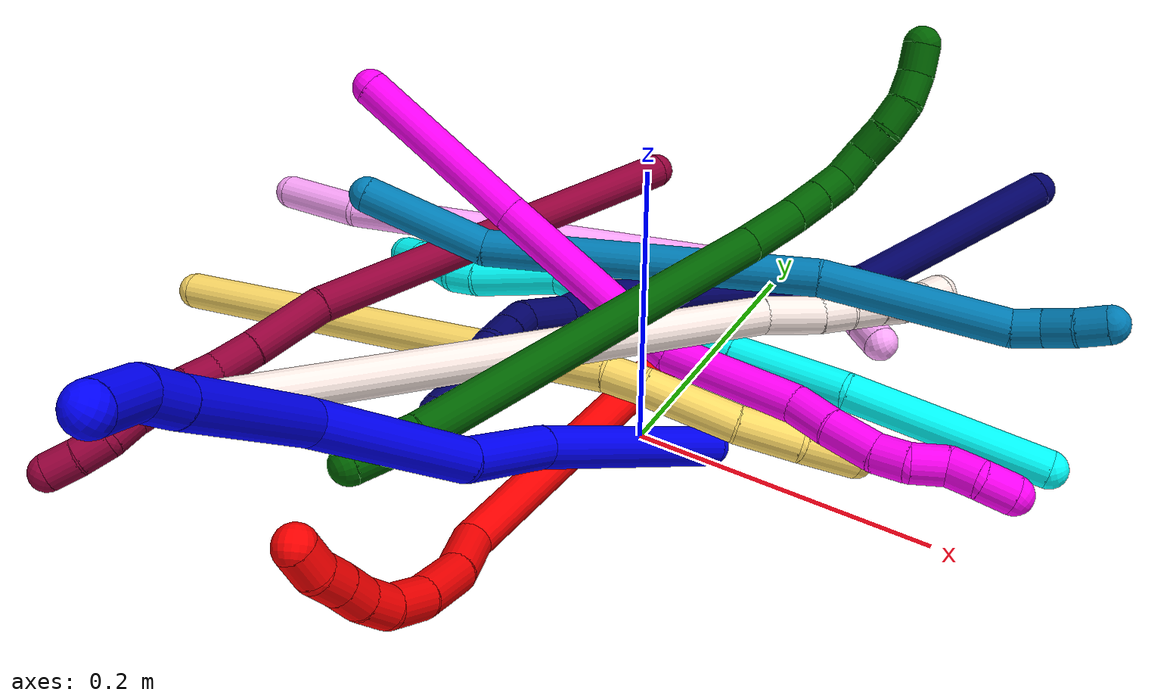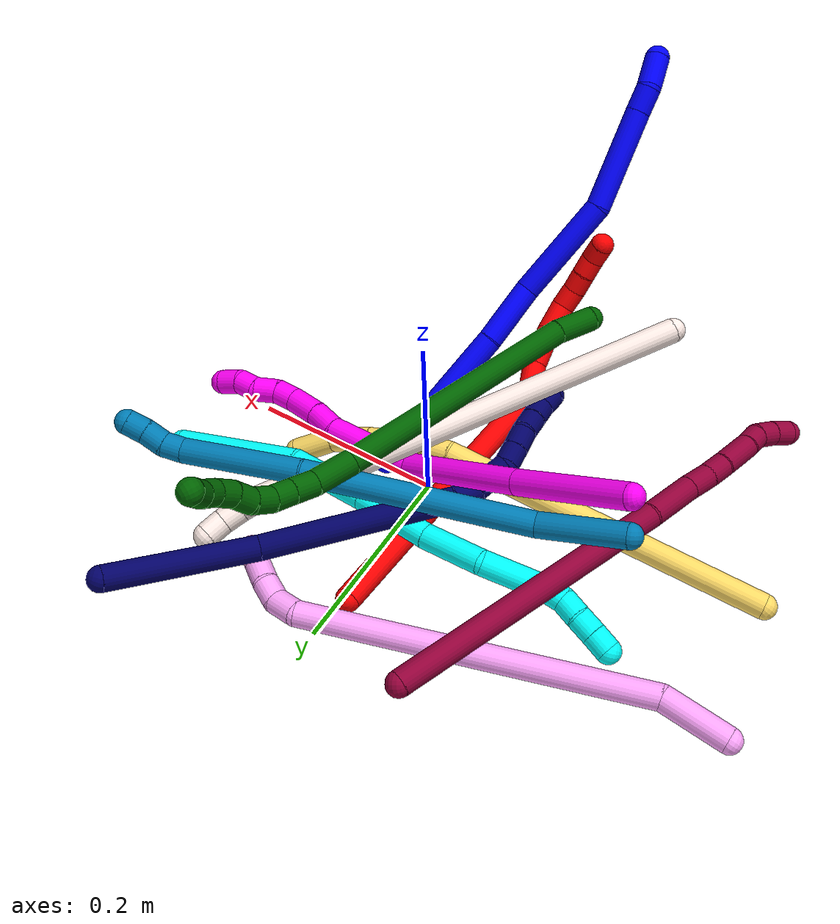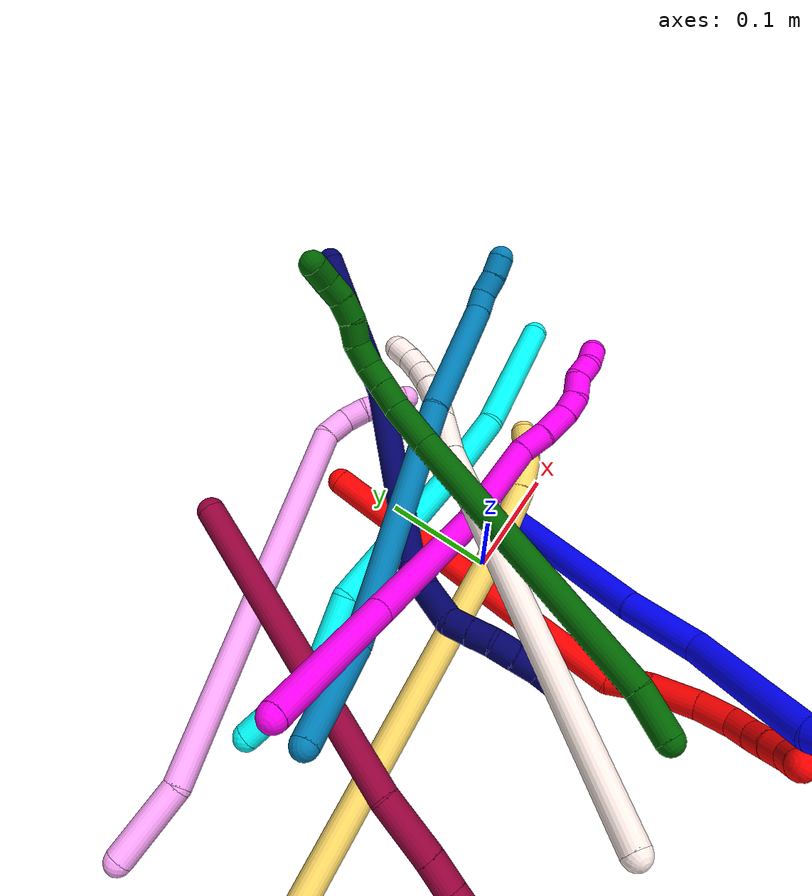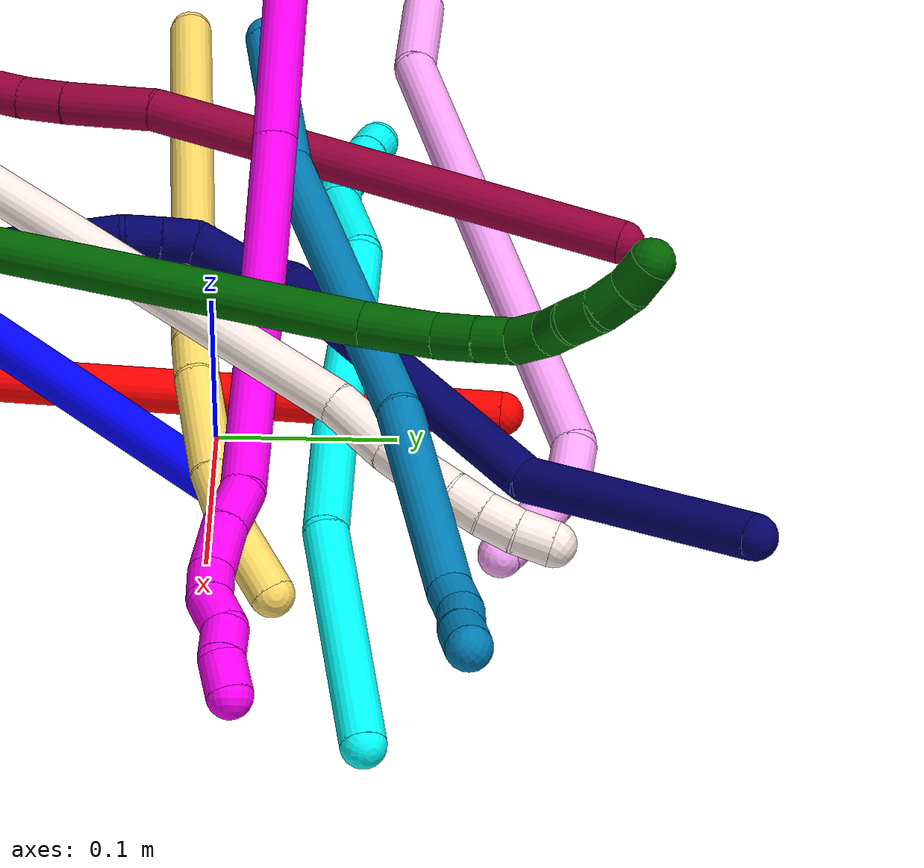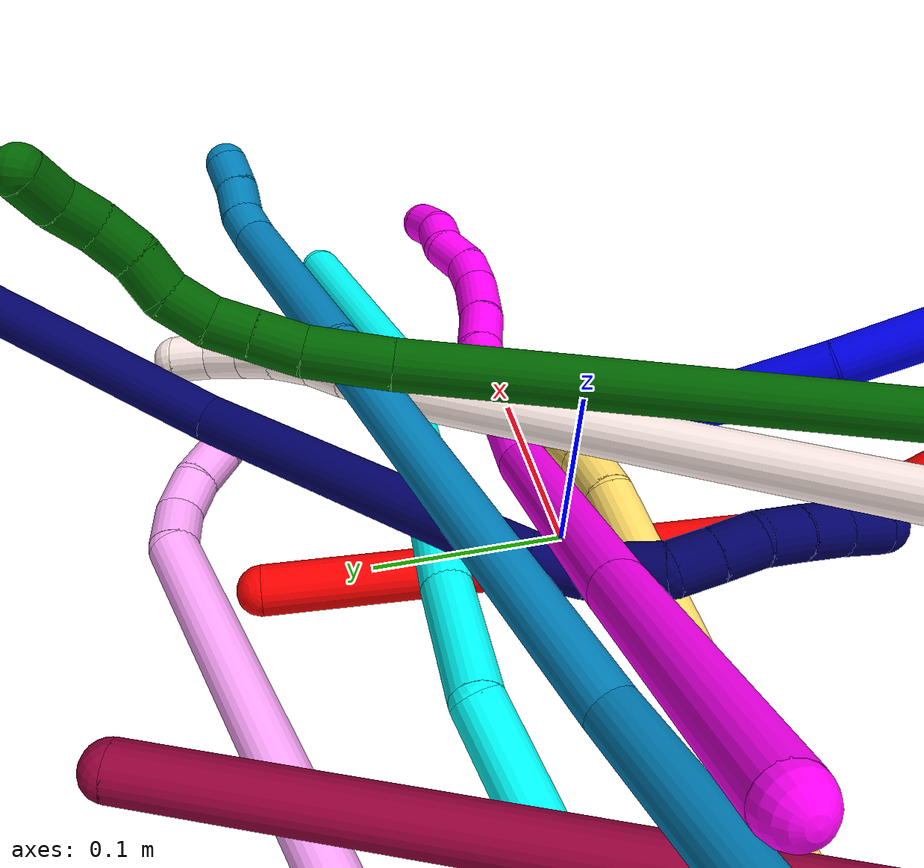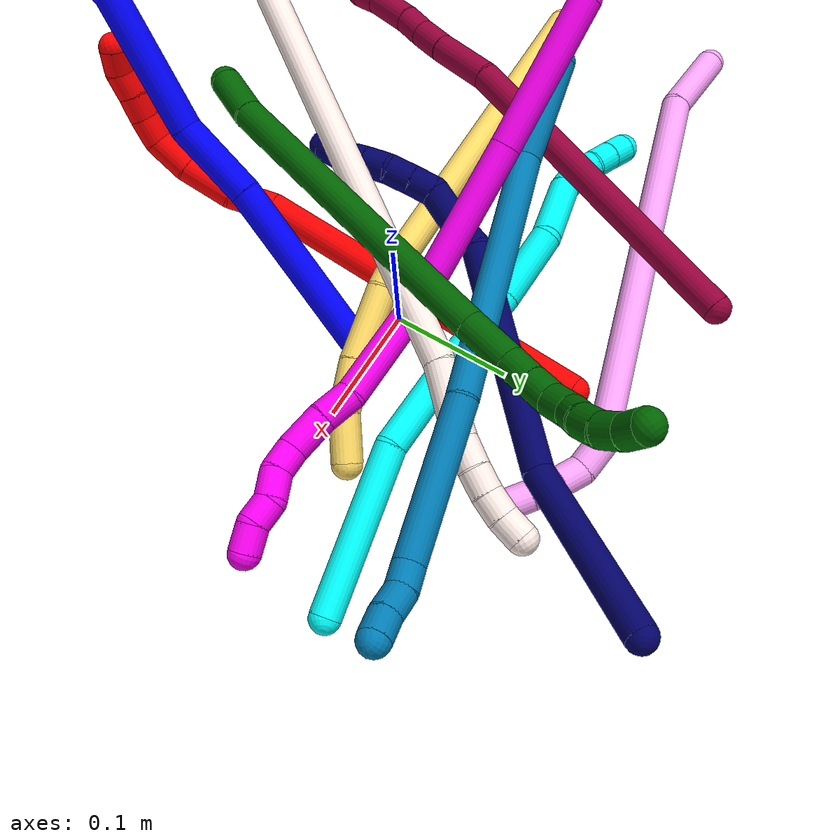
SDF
<sdf version="1.7">
 <world name="default">
  <plugin name="TubeGeneratorPlugin" filename="libtube_generator_plugin.so"/>
  <model name="photoneo_s_sensor">
   <static>1</static>
   <pose>0 0 2 1.57079 1.57079 3.14159</pose>
   <link name="link">
    <inertial><mass>0.1</mass></inertial>
    <sensor name="sensor" type="depth">
     <update_rate>30</update_rate>
     <camera>
      <horizontal_fov>1.22</horizontal_fov>
      <image><width>1920</width><height>1200</height><format>B8G8R8</format></image>
      <clip><near>0.1</near><far>4</far></clip>
      <depth_camera><output>points</output></depth_camera>
     </camera>
     <plugin name="camera_plugin" filename="libgazebo_ros_depth_camera.so">
      <baseline>0.2</baseline>
      <alwaysOn>1</alwaysOn>
      <updateRate>0.0</updateRate>
      <cameraName>camera_ir</cameraName>
      <imageTopicName>/camera/color/image_raw</imageTopicName>
      <cameraInfoTopicName>/camera/color/camera_info</cameraInfoTopicName>
      <depthImageTopicName>/camera/depth/image_raw</depthImageTopicName>
      <depthImageCameraInfoTopicName>/camera/depth/camera_info</depthImageCameraInfoTopicName>
      <pointCloudTopicName>/camera/depth/points</pointCloudTopicName>
      <frameName>fr_optical</frameName>
      <pointCloudCutoff>0.1</pointCloudCutoff>
      <pointCloudCutoffMax>2.0</pointCloudCutoffMax>
      <distortionK1>0</distortionK1>
      <distortionK2>0</distortionK2>
      <distortionK3>0</distortionK3>
      <distortionT1>0</distortionT1>
      <distortionT2>0</distortionT2>
      <CxPrime>0</CxPrime>
      <Cx>0</Cx>
      <Cy>0</Cy>
      <focalLength>0</focalLength>
      <hackBaseline>0</hackBaseline>
     </plugin>
    </sensor>
   </link>
  </model>
  <gravity>0 0 -9.8</gravity>
  <magnetic_field>6e-06 2.3e-05 -4.2e-05</magnetic_field>
  <atmosphere type="adiabatic"/>
  <physics name="default_physics" default="0" type="ode">
   <max_step_size>0.003</max_step_size>
   <real_time_factor>1</real_time_factor>
   <real_time_update_rate>1000</real_time_update_rate>
   <max_contacts>10000</max_contacts>
   <ode>
    <solver>
     <type>quick</type>
     <iters>100</iters>
     <sor>1.3</sor>
     <use_dynamic_moi_rescaling>0</use_dynamic_moi_rescaling>
    </solver>
    <constraints>
     <contact_max_correcting_vel>0</contact_max_correcting_vel>
     <contact_surface_layer>0.001</contact_surface_layer>
     <cfm>0</cfm>
     <erp>0.2</erp>
    </constraints>
   </ode>
  </physics>
  <scene><ambient>0.4 0.4 0.4 1</ambient><background>0.7 0.7 0.7 1</background><shadows>0</shadows></scene>
  <audio><device>default</device></audio>
  <spherical_coordinates>
   <surface_model>EARTH_WGS84</surface_model>
   <latitude_deg>0</latitude_deg>
   <longitude_deg>0</longitude_deg>
   <elevation>0</elevation>
   <heading_deg>0</heading_deg>
  </spherical_coordinates>
  <model name="bin">
   <static>1</static>
   <link name="bottom">
    <collision name="collision-bottom">
     <pose>0 0 -0.01 0 -0 0</pose>
     <geometry><box><size>0.8 0.6 0.02</size></box></geometry>
     <surface>
      <friction><ode><mu>100</mu><mu2>100</mu2></ode></friction>
      <contact><collide_bitmask>65535</collide_bitmask></contact>
     </surface>
    </collision>
   </link>
   <link name="west_wall">
    <collision name="collision-west_wall">
     <pose>-0.41 0 0.1 0 -0 0</pose>
     <geometry><box><size>0.02 0.6 0.2</size></box></geometry>
     <surface>
      <friction><ode><mu>100</mu><mu2>100</mu2></ode></friction>
      <contact><collide_bitmask>65535</collide_bitmask></contact>
     </surface>
    </collision>
   </link>
   <link name="east_wall">
    <collision name="collision-east_wall">
     <pose>0.41 0 0.1 0 -0 0</pose>
     <geometry><box><size>0.02 0.6 0.2</size></box></geometry>
     <surface>
      <friction><ode><mu>100</mu><mu2>100</mu2></ode></friction>
      <contact><collide_bitmask>65535</collide_bitmask></contact>
     </surface>
    </collision>
   </link>
   <link name="south_wall">
    <collision name="collision-south_wall">
     <pose>0 -0.31 0.1 0 -0 0</pose>
     <geometry><box><size>0.8 0.02 0.2</size></box></geometry>
     <surface>
      <friction><ode><mu>100</mu><mu2>100</mu2></ode></friction>
      <contact><collide_bitmask>65535</collide_bitmask></contact>
     </surface>
    </collision>
   </link>
   <link name="north_wall">
    <collision name="collision-north_wall">
     <pose>0 0.31 0.1 0 -0 0</pose>
     <geometry><box><size>0.8 0.02 0.2</size></box></geometry>
     <surface>
      <friction><ode><mu>100</mu><mu2>100</mu2></ode></friction>
      <contact><collide_bitmask>65535</collide_bitmask></contact>
     </surface>
    </collision>
   </link>
  </model>
  <model name="1">
   <static>0</static>
   <link name="1">
    <collision name="collision-cylinder-e_1_1_4">
     <pose>-0.00431 -0.025804 0.076562 0.325081 -0.053291 -0.008741</pose>
     <geometry><cylinder><radius>0.0125</radius><length>0.161817</length></cylinder></geometry>
     <surface>
      <friction><ode><mu>1.16</mu><mu2>1.16</mu2><slip1>0</slip1><slip2>0</slip2></ode></friction>
      <contact><ode><kp>1e+06</kp><kd>1</kd><max_vel>0</max_vel><min_depth>0.001</min_depth></ode></contact>
     </surface>
    </collision>
    <visual name="visual-cylinder-e_1_1_4">
     <pose>-0.00431 -0.025804 0.076562 0.325081 -0.053291 -0.008741</pose>
     <geometry><cylinder><radius>0.0125</radius><length>0.161817</length></cylinder></geometry>
     <material><ambient>0 0 1 1</ambient></material>
    </visual>
    <collision name="collision-cylinder-e_2_4_5">
     <pose>-0.008699 -0.065296 0.182455 0.436613 -0.002466 -0.000547</pose>
     <geometry><cylinder><radius>0.0125</radius><length>0.064734</length></cylinder></geometry>
     <surface>
      <friction><ode><mu>1.16</mu><mu2>1.16</mu2><slip1>0</slip1><slip2>0</slip2></ode></friction>
      <contact><ode><kp>1e+06</kp><kd>1</kd><max_vel>0</max_vel><min_depth>0.001</min_depth></ode></contact>
     </surface>
    </collision>
    <visual name="visual-cylinder-e_2_4_5">
     <pose>-0.008699 -0.065296 0.182455 0.436613 -0.002466 -0.000547</pose>
     <geometry><cylinder><radius>0.0125</radius><length>0.064734</length></cylinder></geometry>
     <material><ambient>0 0 1 1</ambient></material>
    </visual>
    <collision name="collision-cylinder-e_3_5_6">
     <pose>-0.010651 -0.087103 0.265995 0.14868 -0.034134 -0.002542</pose>
     <geometry><cylinder><radius>0.0125</radius><length>0.109693</length></cylinder></geometry>
     <surface>
      <friction><ode><mu>1.16</mu><mu2>1.16</mu2><slip1>0</slip1><slip2>0</slip2></ode></friction>
      <contact><ode><kp>1e+06</kp><kd>1</kd><max_vel>0</max_vel><min_depth>0.001</min_depth></ode></contact>
     </surface>
    </collision>
    <visual name="visual-cylinder-e_3_5_6">
     <pose>-0.010651 -0.087103 0.265995 0.14868 -0.034134 -0.002542</pose>
     <geometry><cylinder><radius>0.0125</radius><length>0.109693</length></cylinder></geometry>
     <material><ambient>0 0 1 1</ambient></material>
    </visual>
    <collision name="collision-cylinder-e_4_6_7">
     <pose>0.000958 -0.109818 0.36773 0.297973 0.264778 0.039971</pose>
     <geometry><cylinder><radius>0.0125</radius><length>0.103022</length></cylinder></geometry>
     <surface>
      <friction><ode><mu>1.16</mu><mu2>1.16</mu2><slip1>0</slip1><slip2>0</slip2></ode></friction>
      <contact><ode><kp>1e+06</kp><kd>1</kd><max_vel>0</max_vel><min_depth>0.001</min_depth></ode></contact>
     </surface>
    </collision>
    <visual name="visual-cylinder-e_4_6_7">
     <pose>0.000958 -0.109818 0.36773 0.297973 0.264778 0.039971</pose>
     <geometry><cylinder><radius>0.0125</radius><length>0.103022</length></cylinder></geometry>
     <material><ambient>0 0 1 1</ambient></material>
    </visual>
    <collision name="collision-cylinder-e_5_7_8">
     <pose>0.017662 -0.127468 0.427609 0.24238 0.248125 0.030372</pose>
     <geometry><cylinder><radius>0.0125</radius><length>0.026255</length></cylinder></geometry>
     <surface>
      <friction><ode><mu>1.16</mu><mu2>1.16</mu2><slip1>0</slip1><slip2>0</slip2></ode></friction>
      <contact><ode><kp>1e+06</kp><kd>1</kd><max_vel>0</max_vel><min_depth>0.001</min_depth></ode></contact>
     </surface>
    </collision>
    <visual name="visual-cylinder-e_5_7_8">
     <pose>0.017662 -0.127468 0.427609 0.24238 0.248125 0.030372</pose>
     <geometry><cylinder><radius>0.0125</radius><length>0.026255</length></cylinder></geometry>
     <material><ambient>0 0 1 1</ambient></material>
    </visual>
    <collision name="collision-cylinder-e_6_8_2">
     <pose>0.02616 -0.140049 0.453328 0.619227 0.310947 0.100198</pose>
     <geometry><cylinder><radius>0.0125</radius><length>0.034478</length></cylinder></geometry>
     <surface>
      <friction><ode><mu>1.16</mu><mu2>1.16</mu2><slip1>0</slip1><slip2>0</slip2></ode></friction>
      <contact><ode><kp>1e+06</kp><kd>1</kd><max_vel>0</max_vel><min_depth>0.001</min_depth></ode></contact>
     </surface>
    </collision>
    <visual name="visual-cylinder-e_6_8_2">
     <pose>0.02616 -0.140049 0.453328 0.619227 0.310947 0.100198</pose>
     <geometry><cylinder><radius>0.0125</radius><length>0.034478</length></cylinder></geometry>
     <material><ambient>0 0 1 1</ambient></material>
    </visual>
    <collision name="collision-sphere-2">
     <pose>0.031435 -0.149574 0.466693 0 -0 0</pose>
     <geometry><sphere><radius>0.0125</radius></sphere></geometry>
     <surface>
      <friction><ode><mu>1.16</mu><mu2>1.16</mu2><slip1>0</slip1><slip2>0</slip2></ode></friction>
      <contact><ode><kp>1e+06</kp><kd>1</kd><max_vel>0</max_vel><min_depth>0.001</min_depth></ode></contact>
     </surface>
    </collision>
    <visual name="visual-sphere-2">
     <pose>0.031435 -0.149574 0.466693 0 -0 0</pose>
     <geometry><sphere><radius>0.0125</radius></sphere></geometry>
     <material><ambient>0 0 1 1</ambient></material>
    </visual>
    <collision name="collision-sphere-4">
     <pose>-0.008619 -0.051609 0.153124 0 -0 0</pose>
     <geometry><sphere><radius>0.0125</radius></sphere></geometry>
     <surface>
      <friction><ode><mu>1.16</mu><mu2>1.16</mu2><slip1>0</slip1><slip2>0</slip2></ode></friction>
      <contact><ode><kp>1e+06</kp><kd>1</kd><max_vel>0</max_vel><min_depth>0.001</min_depth></ode></contact>
     </surface>
    </collision>
    <visual name="visual-sphere-4">
     <pose>-0.008619 -0.051609 0.153124 0 -0 0</pose>
     <geometry><sphere><radius>0.0125</radius></sphere></geometry>
     <material><ambient>0 0 1 1</ambient></material>
    </visual>
    <collision name="collision-sphere-1">
     <geometry><sphere><radius>0.0125</radius></sphere></geometry>
     <surface>
      <friction><ode><mu>1.16</mu><mu2>1.16</mu2><slip1>0</slip1><slip2>0</slip2></ode></friction>
      <contact><ode><kp>1e+06</kp><kd>1</kd><max_vel>0</max_vel><min_depth>0.001</min_depth></ode></contact>
     </surface>
    </collision>
    <visual name="visual-sphere-1">
     <geometry><sphere><radius>0.0125</radius></sphere></geometry>
     <material><ambient>0 0 1 1</ambient></material>
    </visual>
    <collision name="collision-sphere-8">
     <pose>0.020886 -0.130523 0.439962 0 -0 0</pose>
     <geometry><sphere><radius>0.0125</radius></sphere></geometry>
     <surface>
      <friction><ode><mu>1.16</mu><mu2>1.16</mu2><slip1>0</slip1><slip2>0</slip2></ode></friction>
      <contact><ode><kp>1e+06</kp><kd>1</kd><max_vel>0</max_vel><min_depth>0.001</min_depth></ode></contact>
     </surface>
    </collision>
    <visual name="visual-sphere-8">
     <pose>0.020886 -0.130523 0.439962 0 -0 0</pose>
     <geometry><sphere><radius>0.0125</radius></sphere></geometry>
     <material><ambient>0 0 1 1</ambient></material>
    </visual>
    <collision name="collision-sphere-5">
     <pose>-0.008779 -0.078983 0.211785 0 -0 0</pose>
     <geometry><sphere><radius>0.0125</radius></sphere></geometry>
     <surface>
      <friction><ode><mu>1.16</mu><mu2>1.16</mu2><slip1>0</slip1><slip2>0</slip2></ode></friction>
      <contact><ode><kp>1e+06</kp><kd>1</kd><max_vel>0</max_vel><min_depth>0.001</min_depth></ode></contact>
     </surface>
    </collision>
    <visual name="visual-sphere-5">
     <pose>-0.008779 -0.078983 0.211785 0 -0 0</pose>
     <geometry><sphere><radius>0.0125</radius></sphere></geometry>
     <material><ambient>0 0 1 1</ambient></material>
    </visual>
    <collision name="collision-sphere-6">
     <pose>-0.012523 -0.095222 0.320205 0 -0 0</pose>
     <geometry><sphere><radius>0.0125</radius></sphere></geometry>
     <surface>
      <friction><ode><mu>1.16</mu><mu2>1.16</mu2><slip1>0</slip1><slip2>0</slip2></ode></friction>
      <contact><ode><kp>1e+06</kp><kd>1</kd><max_vel>0</max_vel><min_depth>0.001</min_depth></ode></contact>
     </surface>
    </collision>
    <visual name="visual-sphere-6">
     <pose>-0.012523 -0.095222 0.320205 0 -0 0</pose>
     <geometry><sphere><radius>0.0125</radius></sphere></geometry>
     <material><ambient>0 0 1 1</ambient></material>
    </visual>
    <collision name="collision-sphere-7">
     <pose>0.014438 -0.124414 0.415255 0 -0 0</pose>
     <geometry><sphere><radius>0.0125</radius></sphere></geometry>
     <surface>
      <friction><ode><mu>1.16</mu><mu2>1.16</mu2><slip1>0</slip1><slip2>0</slip2></ode></friction>
      <contact><ode><kp>1e+06</kp><kd>1</kd><max_vel>0</max_vel><min_depth>0.001</min_depth></ode></contact>
     </surface>
    </collision>
    <visual name="visual-sphere-7">
     <pose>0.014438 -0.124414 0.415255 0 -0 0</pose>
     <geometry><sphere><radius>0.0125</radius></sphere></geometry>
     <material><ambient>0 0 1 1</ambient></material>
    </visual>
    <inertial>
     <pose>-0.001929 -0.074892 0.236239 0 -0 0</pose>
     <mass>0.5</mass>
     <inertia><ixx>0.0006</ixx><ixy>0</ixy><ixz>0</ixz><iyy>0.000563</iyy><iyz>0</iyz><izz>0.000205</izz></inertia>
    </inertial>
   </link>
   <pose>0.049012 0.001497 0.011442 0.593682 -0.531475 0.116836</pose>
  </model>
  <model name="2">
   <static>0</static>
   <link name="2">
    <collision name="collision-cylinder-e_1_1_4">
     <pose>0.024232 -0.108801 0.104735 0.804436 0.159099 0.067799</pose>
     <geometry><cylinder><radius>0.0125</radius><length>0.305905</length></cylinder></geometry>
     <surface>
      <friction><ode><mu>1.16</mu><mu2>1.16</mu2><slip1>0</slip1><slip2>0</slip2></ode></friction>
      <contact><ode><kp>1e+06</kp><kd>1</kd><max_vel>0</max_vel><min_depth>0.001</min_depth></ode></contact>
     </surface>
    </collision>
    <visual name="visual-cylinder-e_1_1_4">
     <pose>0.024232 -0.108801 0.104735 0.804436 0.159099 0.067799</pose>
     <geometry><cylinder><radius>0.0125</radius><length>0.305905</length></cylinder></geometry>
     <material><ambient>1 0 0 1</ambient></material>
    </visual>
    <collision name="collision-cylinder-e_2_4_5">
     <pose>0.042348 -0.231745 0.220774 0.89653 -0.325789 -0.15775</pose>
     <geometry><cylinder><radius>0.0125</radius><length>0.038219</length></cylinder></geometry>
     <surface>
      <friction><ode><mu>1.16</mu><mu2>1.16</mu2><slip1>0</slip1><slip2>0</slip2></ode></friction>
      <contact><ode><kp>1e+06</kp><kd>1</kd><max_vel>0</max_vel><min_depth>0.001</min_depth></ode></contact>
     </surface>
    </collision>
    <visual name="visual-cylinder-e_2_4_5">
     <pose>0.042348 -0.231745 0.220774 0.89653 -0.325789 -0.15775</pose>
     <geometry><cylinder><radius>0.0125</radius><length>0.038219</length></cylinder></geometry>
     <material><ambient>1 0 0 1</ambient></material>
    </visual>
    <collision name="collision-cylinder-e_3_5_6">
     <pose>0.03287 -0.264409 0.241498 1.10022 -0.160414 -0.098507</pose>
     <geometry><cylinder><radius>0.0125</radius><length>0.042102</length></cylinder></geometry>
     <surface>
      <friction><ode><mu>1.16</mu><mu2>1.16</mu2><slip1>0</slip1><slip2>0</slip2></ode></friction>
      <contact><ode><kp>1e+06</kp><kd>1</kd><max_vel>0</max_vel><min_depth>0.001</min_depth></ode></contact>
     </surface>
    </collision>
    <visual name="visual-cylinder-e_3_5_6">
     <pose>0.03287 -0.264409 0.241498 1.10022 -0.160414 -0.098507</pose>
     <geometry><cylinder><radius>0.0125</radius><length>0.042102</length></cylinder></geometry>
     <material><ambient>1 0 0 1</ambient></material>
    </visual>
    <collision name="collision-cylinder-e_4_6_7">
     <pose>0.028583 -0.29781 0.255263 1.28683 -0.059545 -0.044657</pose>
     <geometry><cylinder><radius>0.0125</radius><length>0.031055</length></cylinder></geometry>
     <surface>
      <friction><ode><mu>1.16</mu><mu2>1.16</mu2><slip1>0</slip1><slip2>0</slip2></ode></friction>
      <contact><ode><kp>1e+06</kp><kd>1</kd><max_vel>0</max_vel><min_depth>0.001</min_depth></ode></contact>
     </surface>
    </collision>
    <visual name="visual-cylinder-e_4_6_7">
     <pose>0.028583 -0.29781 0.255263 1.28683 -0.059545 -0.044657</pose>
     <geometry><cylinder><radius>0.0125</radius><length>0.031055</length></cylinder></geometry>
     <material><ambient>1 0 0 1</ambient></material>
    </visual>
    <collision name="collision-cylinder-e_5_7_8">
     <pose>0.02772 -0.323803 0.258746 1.64798 0.005427 0.005863</pose>
     <geometry><cylinder><radius>0.0125</radius><length>0.022295</length></cylinder></geometry>
     <surface>
      <friction><ode><mu>1.16</mu><mu2>1.16</mu2><slip1>0</slip1><slip2>0</slip2></ode></friction>
      <contact><ode><kp>1e+06</kp><kd>1</kd><max_vel>0</max_vel><min_depth>0.001</min_depth></ode></contact>
     </surface>
    </collision>
    <visual name="visual-cylinder-e_5_7_8">
     <pose>0.02772 -0.323803 0.258746 1.64798 0.005427 0.005863</pose>
     <geometry><cylinder><radius>0.0125</radius><length>0.022295</length></cylinder></geometry>
     <material><ambient>1 0 0 1</ambient></material>
    </visual>
    <collision name="collision-cylinder-e_6_8_9">
     <pose>0.027132 -0.344774 0.255403 1.81755 -0.063695 -0.081711</pose>
     <geometry><cylinder><radius>0.0125</radius><length>0.020371</length></cylinder></geometry>
     <surface>
      <friction><ode><mu>1.16</mu><mu2>1.16</mu2><slip1>0</slip1><slip2>0</slip2></ode></friction>
      <contact><ode><kp>1e+06</kp><kd>1</kd><max_vel>0</max_vel><min_depth>0.001</min_depth></ode></contact>
     </surface>
    </collision>
    <visual name="visual-cylinder-e_6_8_9">
     <pose>0.027132 -0.344774 0.255403 1.81755 -0.063695 -0.081711</pose>
     <geometry><cylinder><radius>0.0125</radius><length>0.020371</length></cylinder></geometry>
     <material><ambient>1 0 0 1</ambient></material>
    </visual>
    <collision name="collision-cylinder-e_7_9_10">
     <pose>0.025874 -0.364462 0.251177 1.74629 -0.060968 -0.07272</pose>
     <geometry><cylinder><radius>0.0125</radius><length>0.020006</length></cylinder></geometry>
     <surface>
      <friction><ode><mu>1.16</mu><mu2>1.16</mu2><slip1>0</slip1><slip2>0</slip2></ode></friction>
      <contact><ode><kp>1e+06</kp><kd>1</kd><max_vel>0</max_vel><min_depth>0.001</min_depth></ode></contact>
     </surface>
    </collision>
    <visual name="visual-cylinder-e_7_9_10">
     <pose>0.025874 -0.364462 0.251177 1.74629 -0.060968 -0.07272</pose>
     <geometry><cylinder><radius>0.0125</radius><length>0.020006</length></cylinder></geometry>
     <material><ambient>1 0 0 1</ambient></material>
    </visual>
    <collision name="collision-cylinder-e_8_10_2">
     <pose>0.025008 -0.382971 0.244423 2.09449 -0.02557 -0.044289</pose>
     <geometry><cylinder><radius>0.0125</radius><length>0.020049</length></cylinder></geometry>
     <surface>
      <friction><ode><mu>1.16</mu><mu2>1.16</mu2><slip1>0</slip1><slip2>0</slip2></ode></friction>
      <contact><ode><kp>1e+06</kp><kd>1</kd><max_vel>0</max_vel><min_depth>0.001</min_depth></ode></contact>
     </surface>
    </collision>
    <visual name="visual-cylinder-e_8_10_2">
     <pose>0.025008 -0.382971 0.244423 2.09449 -0.02557 -0.044289</pose>
     <geometry><cylinder><radius>0.0125</radius><length>0.020049</length></cylinder></geometry>
     <material><ambient>1 0 0 1</ambient></material>
    </visual>
    <collision name="collision-sphere-2">
     <pose>0.024752 -0.391649 0.239411 0 -0 0</pose>
     <geometry><sphere><radius>0.0125</radius></sphere></geometry>
     <surface>
      <friction><ode><mu>1.16</mu><mu2>1.16</mu2><slip1>0</slip1><slip2>0</slip2></ode></friction>
      <contact><ode><kp>1e+06</kp><kd>1</kd><max_vel>0</max_vel><min_depth>0.001</min_depth></ode></contact>
     </surface>
    </collision>
    <visual name="visual-sphere-2">
     <pose>0.024752 -0.391649 0.239411 0 -0 0</pose>
     <geometry><sphere><radius>0.0125</radius></sphere></geometry>
     <material><ambient>1 0 0 1</ambient></material>
    </visual>
    <collision name="collision-sphere-10">
     <pose>0.025264 -0.374293 0.249434 0 -0 0</pose>
     <geometry><sphere><radius>0.0125</radius></sphere></geometry>
     <surface>
      <friction><ode><mu>1.16</mu><mu2>1.16</mu2><slip1>0</slip1><slip2>0</slip2></ode></friction>
      <contact><ode><kp>1e+06</kp><kd>1</kd><max_vel>0</max_vel><min_depth>0.001</min_depth></ode></contact>
     </surface>
    </collision>
    <visual name="visual-sphere-10">
     <pose>0.025264 -0.374293 0.249434 0 -0 0</pose>
     <geometry><sphere><radius>0.0125</radius></sphere></geometry>
     <material><ambient>1 0 0 1</ambient></material>
    </visual>
    <collision name="collision-sphere-9">
     <pose>0.026483 -0.354631 0.252921 0 -0 0</pose>
     <geometry><sphere><radius>0.0125</radius></sphere></geometry>
     <surface>
      <friction><ode><mu>1.16</mu><mu2>1.16</mu2><slip1>0</slip1><slip2>0</slip2></ode></friction>
      <contact><ode><kp>1e+06</kp><kd>1</kd><max_vel>0</max_vel><min_depth>0.001</min_depth></ode></contact>
     </surface>
    </collision>
    <visual name="visual-sphere-9">
     <pose>0.026483 -0.354631 0.252921 0 -0 0</pose>
     <geometry><sphere><radius>0.0125</radius></sphere></geometry>
     <material><ambient>1 0 0 1</ambient></material>
    </visual>
    <collision name="collision-sphere-4">
     <pose>0.048464 -0.217602 0.209471 0 -0 0</pose>
     <geometry><sphere><radius>0.0125</radius></sphere></geometry>
     <surface>
      <friction><ode><mu>1.16</mu><mu2>1.16</mu2><slip1>0</slip1><slip2>0</slip2></ode></friction>
      <contact><ode><kp>1e+06</kp><kd>1</kd><max_vel>0</max_vel><min_depth>0.001</min_depth></ode></contact>
     </surface>
    </collision>
    <visual name="visual-sphere-4">
     <pose>0.048464 -0.217602 0.209471 0 -0 0</pose>
     <geometry><sphere><radius>0.0125</radius></sphere></geometry>
     <material><ambient>1 0 0 1</ambient></material>
    </visual>
    <collision name="collision-sphere-1">
     <geometry><sphere><radius>0.0125</radius></sphere></geometry>
     <surface>
      <friction><ode><mu>1.16</mu><mu2>1.16</mu2><slip1>0</slip1><slip2>0</slip2></ode></friction>
      <contact><ode><kp>1e+06</kp><kd>1</kd><max_vel>0</max_vel><min_depth>0.001</min_depth></ode></contact>
     </surface>
    </collision>
    <visual name="visual-sphere-1">
     <geometry><sphere><radius>0.0125</radius></sphere></geometry>
     <material><ambient>1 0 0 1</ambient></material>
    </visual>
    <collision name="collision-sphere-8">
     <pose>0.02778 -0.334918 0.257886 0 -0 0</pose>
     <geometry><sphere><radius>0.0125</radius></sphere></geometry>
     <surface>
      <friction><ode><mu>1.16</mu><mu2>1.16</mu2><slip1>0</slip1><slip2>0</slip2></ode></friction>
      <contact><ode><kp>1e+06</kp><kd>1</kd><max_vel>0</max_vel><min_depth>0.001</min_depth></ode></contact>
     </surface>
    </collision>
    <visual name="visual-sphere-8">
     <pose>0.02778 -0.334918 0.257886 0 -0 0</pose>
     <geometry><sphere><radius>0.0125</radius></sphere></geometry>
     <material><ambient>1 0 0 1</ambient></material>
    </visual>
    <collision name="collision-sphere-5">
     <pose>0.036232 -0.245887 0.232077 0 -0 0</pose>
     <geometry><sphere><radius>0.0125</radius></sphere></geometry>
     <surface>
      <friction><ode><mu>1.16</mu><mu2>1.16</mu2><slip1>0</slip1><slip2>0</slip2></ode></friction>
      <contact><ode><kp>1e+06</kp><kd>1</kd><max_vel>0</max_vel><min_depth>0.001</min_depth></ode></contact>
     </surface>
    </collision>
    <visual name="visual-sphere-5">
     <pose>0.036232 -0.245887 0.232077 0 -0 0</pose>
     <geometry><sphere><radius>0.0125</radius></sphere></geometry>
     <material><ambient>1 0 0 1</ambient></material>
    </visual>
    <collision name="collision-sphere-6">
     <pose>0.029507 -0.282931 0.25092 0 -0 0</pose>
     <geometry><sphere><radius>0.0125</radius></sphere></geometry>
     <surface>
      <friction><ode><mu>1.16</mu><mu2>1.16</mu2><slip1>0</slip1><slip2>0</slip2></ode></friction>
      <contact><ode><kp>1e+06</kp><kd>1</kd><max_vel>0</max_vel><min_depth>0.001</min_depth></ode></contact>
     </surface>
    </collision>
    <visual name="visual-sphere-6">
     <pose>0.029507 -0.282931 0.25092 0 -0 0</pose>
     <geometry><sphere><radius>0.0125</radius></sphere></geometry>
     <material><ambient>1 0 0 1</ambient></material>
    </visual>
    <collision name="collision-sphere-7">
     <pose>0.027659 -0.312689 0.259605 0 -0 0</pose>
     <geometry><sphere><radius>0.0125</radius></sphere></geometry>
     <surface>
      <friction><ode><mu>1.16</mu><mu2>1.16</mu2><slip1>0</slip1><slip2>0</slip2></ode></friction>
      <contact><ode><kp>1e+06</kp><kd>1</kd><max_vel>0</max_vel><min_depth>0.001</min_depth></ode></contact>
     </surface>
    </collision>
    <visual name="visual-sphere-7">
     <pose>0.027659 -0.312689 0.259605 0 -0 0</pose>
     <geometry><sphere><radius>0.0125</radius></sphere></geometry>
     <material><ambient>1 0 0 1</ambient></material>
    </visual>
    <inertial>
     <pose>0.026985 -0.183464 0.158936 0 -0 0</pose>
     <mass>0.5</mass>
     <inertia>
      <ixx>0.002545</ixx>
      <ixy>0</ixy>
      <ixz>0</ixz>
      <iyy>0.001812</iyy>
      <iyz>0</iyz>
      <izz>0.001369</izz>
     </inertia>
    </inertial>
   </link>
   <pose>-0.010569 0.157301 0.011487 -2.30665 0.396255 -3.0405</pose>
  </model>
  <model name="3">
   <static>0</static>
   <link name="3">
    <collision name="collision-cylinder-e_1_1_4">
     <pose>-0.025102 0.026182 0.056056 -0.436952 -0.38543 0.086594</pose>
     <geometry><cylinder><radius>0.0125</radius><length>0.133534</length></cylinder></geometry>
     <surface>
      <friction><ode><mu>1.16</mu><mu2>1.16</mu2><slip1>0</slip1><slip2>0</slip2></ode></friction>
      <contact><ode><kp>1e+06</kp><kd>1</kd><max_vel>0</max_vel><min_depth>0.001</min_depth></ode></contact>
     </surface>
    </collision>
    <visual name="visual-cylinder-e_1_1_4">
     <pose>-0.025102 0.026182 0.056056 -0.436952 -0.38543 0.086594</pose>
     <geometry><cylinder><radius>0.0125</radius><length>0.133534</length></cylinder></geometry>
     <material><ambient>0.003922 1 0.996078 1</ambient></material>
    </visual>
    <collision name="collision-cylinder-e_2_4_5">
     <pose>-0.070972 0.057264 0.146161 -0.142941 -0.543179 0.039867</pose>
     <geometry><cylinder><radius>0.0125</radius><length>0.080367</length></cylinder></geometry>
     <surface>
      <friction><ode><mu>1.16</mu><mu2>1.16</mu2><slip1>0</slip1><slip2>0</slip2></ode></friction>
      <contact><ode><kp>1e+06</kp><kd>1</kd><max_vel>0</max_vel><min_depth>0.001</min_depth></ode></contact>
     </surface>
    </collision>
    <visual name="visual-cylinder-e_2_4_5">
     <pose>-0.070972 0.057264 0.146161 -0.142941 -0.543179 0.039867</pose>
     <geometry><cylinder><radius>0.0125</radius><length>0.080367</length></cylinder></geometry>
     <material><ambient>0.003922 1 0.996078 1</ambient></material>
    </visual>
    <collision name="collision-cylinder-e_3_5_6">
     <pose>-0.113722 0.066844 0.211591 -0.148034 -0.605857 0.046344</pose>
     <geometry><cylinder><radius>0.0125</radius><length>0.077197</length></cylinder></geometry>
     <surface>
      <friction><ode><mu>1.16</mu><mu2>1.16</mu2><slip1>0</slip1><slip2>0</slip2></ode></friction>
      <contact><ode><kp>1e+06</kp><kd>1</kd><max_vel>0</max_vel><min_depth>0.001</min_depth></ode></contact>
     </surface>
    </collision>
    <visual name="visual-cylinder-e_3_5_6">
     <pose>-0.113722 0.066844 0.211591 -0.148034 -0.605857 0.046344</pose>
     <geometry><cylinder><radius>0.0125</radius><length>0.077197</length></cylinder></geometry>
     <material><ambient>0.003922 1 0.996078 1</ambient></material>
    </visual>
    <collision name="collision-cylinder-e_4_6_7">
     <pose>-0.153554 0.079551 0.267928 -0.311218 -0.597825 0.096607</pose>
     <geometry><cylinder><radius>0.0125</radius><length>0.063431</length></cylinder></geometry>
     <surface>
      <friction><ode><mu>1.16</mu><mu2>1.16</mu2><slip1>0</slip1><slip2>0</slip2></ode></friction>
      <contact><ode><kp>1e+06</kp><kd>1</kd><max_vel>0</max_vel><min_depth>0.001</min_depth></ode></contact>
     </surface>
    </collision>
    <visual name="visual-cylinder-e_4_6_7">
     <pose>-0.153554 0.079551 0.267928 -0.311218 -0.597825 0.096607</pose>
     <geometry><cylinder><radius>0.0125</radius><length>0.063431</length></cylinder></geometry>
     <material><ambient>0.003922 1 0.996078 1</ambient></material>
    </visual>
    <collision name="collision-cylinder-e_5_7_8">
     <pose>-0.179062 0.087745 0.323614 -0.005409 -0.244207 0.000664</pose>
     <geometry><cylinder><radius>0.0125</radius><length>0.06334</length></cylinder></geometry>
     <surface>
      <friction><ode><mu>1.16</mu><mu2>1.16</mu2><slip1>0</slip1><slip2>0</slip2></ode></friction>
      <contact><ode><kp>1e+06</kp><kd>1</kd><max_vel>0</max_vel><min_depth>0.001</min_depth></ode></contact>
     </surface>
    </collision>
    <visual name="visual-cylinder-e_5_7_8">
     <pose>-0.179062 0.087745 0.323614 -0.005409 -0.244207 0.000664</pose>
     <geometry><cylinder><radius>0.0125</radius><length>0.06334</length></cylinder></geometry>
     <material><ambient>0.003922 1 0.996078 1</ambient></material>
    </visual>
    <collision name="collision-cylinder-e_6_8_9">
     <pose>-0.191279 0.087695 0.363242 0.024271 -0.473381 -0.005855</pose>
     <geometry><cylinder><radius>0.0125</radius><length>0.020002</length></cylinder></geometry>
     <surface>
      <friction><ode><mu>1.16</mu><mu2>1.16</mu2><slip1>0</slip1><slip2>0</slip2></ode></friction>
      <contact><ode><kp>1e+06</kp><kd>1</kd><max_vel>0</max_vel><min_depth>0.001</min_depth></ode></contact>
     </surface>
    </collision>
    <visual name="visual-cylinder-e_6_8_9">
     <pose>-0.191279 0.087695 0.363242 0.024271 -0.473381 -0.005855</pose>
     <geometry><cylinder><radius>0.0125</radius><length>0.020002</length></cylinder></geometry>
     <material><ambient>0.003922 1 0.996078 1</ambient></material>
    </visual>
    <collision name="collision-cylinder-e_7_9_10">
     <pose>-0.204028 0.08678 0.379196 0.09876 -0.857241 -0.045158</pose>
     <geometry><cylinder><radius>0.0125</radius><length>0.021665</length></cylinder></geometry>
     <surface>
      <friction><ode><mu>1.16</mu><mu2>1.16</mu2><slip1>0</slip1><slip2>0</slip2></ode></friction>
      <contact><ode><kp>1e+06</kp><kd>1</kd><max_vel>0</max_vel><min_depth>0.001</min_depth></ode></contact>
     </surface>
    </collision>
    <visual name="visual-cylinder-e_7_9_10">
     <pose>-0.204028 0.08678 0.379196 0.09876 -0.857241 -0.045158</pose>
     <geometry><cylinder><radius>0.0125</radius><length>0.021665</length></cylinder></geometry>
     <material><ambient>0.003922 1 0.996078 1</ambient></material>
    </visual>
    <collision name="collision-cylinder-e_8_10_11">
     <pose>-0.218861 0.08429 0.393816 0.232399 -0.70715 -0.08611</pose>
     <geometry><cylinder><radius>0.0125</radius><length>0.020449</length></cylinder></geometry>
     <surface>
      <friction><ode><mu>1.16</mu><mu2>1.16</mu2><slip1>0</slip1><slip2>0</slip2></ode></friction>
      <contact><ode><kp>1e+06</kp><kd>1</kd><max_vel>0</max_vel><min_depth>0.001</min_depth></ode></contact>
     </surface>
    </collision>
    <visual name="visual-cylinder-e_8_10_11">
     <pose>-0.218861 0.08429 0.393816 0.232399 -0.70715 -0.08611</pose>
     <geometry><cylinder><radius>0.0125</radius><length>0.020449</length></cylinder></geometry>
     <material><ambient>0.003922 1 0.996078 1</ambient></material>
    </visual>
    <collision name="collision-cylinder-e_9_11_2">
     <pose>-0.231938 0.080363 0.40874 0.282581 -0.698435 -0.103497</pose>
     <geometry><cylinder><radius>0.0125</radius><length>0.020015</length></cylinder></geometry>
     <surface>
      <friction><ode><mu>1.16</mu><mu2>1.16</mu2><slip1>0</slip1><slip2>0</slip2></ode></friction>
      <contact><ode><kp>1e+06</kp><kd>1</kd><max_vel>0</max_vel><min_depth>0.001</min_depth></ode></contact>
     </surface>
    </collision>
    <visual name="visual-cylinder-e_9_11_2">
     <pose>-0.231938 0.080363 0.40874 0.282581 -0.698435 -0.103497</pose>
     <geometry><cylinder><radius>0.0125</radius><length>0.020015</length></cylinder></geometry>
     <material><ambient>0.003922 1 0.996078 1</ambient></material>
    </visual>
    <collision name="collision-sphere-2">
     <pose>-0.238373 0.078226 0.4161 0 -0 0</pose>
     <geometry><sphere><radius>0.0125</radius></sphere></geometry>
     <surface>
      <friction><ode><mu>1.16</mu><mu2>1.16</mu2><slip1>0</slip1><slip2>0</slip2></ode></friction>
      <contact><ode><kp>1e+06</kp><kd>1</kd><max_vel>0</max_vel><min_depth>0.001</min_depth></ode></contact>
     </surface>
    </collision>
    <visual name="visual-sphere-2">
     <pose>-0.238373 0.078226 0.4161 0 -0 0</pose>
     <geometry><sphere><radius>0.0125</radius></sphere></geometry>
     <material><ambient>0.003922 1 0.996078 1</ambient></material>
    </visual>
    <collision name="collision-sphere-11">
     <pose>-0.225503 0.0825 0.40138 0 -0 0</pose>
     <geometry><sphere><radius>0.0125</radius></sphere></geometry>
     <surface>
      <friction><ode><mu>1.16</mu><mu2>1.16</mu2><slip1>0</slip1><slip2>0</slip2></ode></friction>
      <contact><ode><kp>1e+06</kp><kd>1</kd><max_vel>0</max_vel><min_depth>0.001</min_depth></ode></contact>
     </surface>
    </collision>
    <visual name="visual-sphere-11">
     <pose>-0.225503 0.0825 0.40138 0 -0 0</pose>
     <geometry><sphere><radius>0.0125</radius></sphere></geometry>
     <material><ambient>0.003922 1 0.996078 1</ambient></material>
    </visual>
    <collision name="collision-sphere-10">
     <pose>-0.212218 0.086081 0.386252 0 -0 0</pose>
     <geometry><sphere><radius>0.0125</radius></sphere></geometry>
     <surface>
      <friction><ode><mu>1.16</mu><mu2>1.16</mu2><slip1>0</slip1><slip2>0</slip2></ode></friction>
      <contact><ode><kp>1e+06</kp><kd>1</kd><max_vel>0</max_vel><min_depth>0.001</min_depth></ode></contact>
     </surface>
    </collision>
    <visual name="visual-sphere-10">
     <pose>-0.212218 0.086081 0.386252 0 -0 0</pose>
     <geometry><sphere><radius>0.0125</radius></sphere></geometry>
     <material><ambient>0.003922 1 0.996078 1</ambient></material>
    </visual>
    <collision name="collision-sphere-9">
     <pose>-0.195838 0.087479 0.37214 0 -0 0</pose>
     <geometry><sphere><radius>0.0125</radius></sphere></geometry>
     <surface>
      <friction><ode><mu>1.16</mu><mu2>1.16</mu2><slip1>0</slip1><slip2>0</slip2></ode></friction>
      <contact><ode><kp>1e+06</kp><kd>1</kd><max_vel>0</max_vel><min_depth>0.001</min_depth></ode></contact>
     </surface>
    </collision>
    <visual name="visual-sphere-9">
     <pose>-0.195838 0.087479 0.37214 0 -0 0</pose>
     <geometry><sphere><radius>0.0125</radius></sphere></geometry>
     <material><ambient>0.003922 1 0.996078 1</ambient></material>
    </visual>
    <collision name="collision-sphere-4">
     <pose>-0.050203 0.052363 0.112112 0 -0 0</pose>
     <geometry><sphere><radius>0.0125</radius></sphere></geometry>
     <surface>
      <friction><ode><mu>1.16</mu><mu2>1.16</mu2><slip1>0</slip1><slip2>0</slip2></ode></friction>
      <contact><ode><kp>1e+06</kp><kd>1</kd><max_vel>0</max_vel><min_depth>0.001</min_depth></ode></contact>
     </surface>
    </collision>
    <visual name="visual-sphere-4">
     <pose>-0.050203 0.052363 0.112112 0 -0 0</pose>
     <geometry><sphere><radius>0.0125</radius></sphere></geometry>
     <material><ambient>0.003922 1 0.996078 1</ambient></material>
    </visual>
    <collision name="collision-sphere-1">
     <geometry><sphere><radius>0.0125</radius></sphere></geometry>
     <surface>
      <friction><ode><mu>1.16</mu><mu2>1.16</mu2><slip1>0</slip1><slip2>0</slip2></ode></friction>
      <contact><ode><kp>1e+06</kp><kd>1</kd><max_vel>0</max_vel><min_depth>0.001</min_depth></ode></contact>
     </surface>
    </collision>
    <visual name="visual-sphere-1">
     <geometry><sphere><radius>0.0125</radius></sphere></geometry>
     <material><ambient>0.003922 1 0.996078 1</ambient></material>
    </visual>
    <collision name="collision-sphere-8">
     <pose>-0.186719 0.087911 0.354343 0 -0 0</pose>
     <geometry><sphere><radius>0.0125</radius></sphere></geometry>
     <surface>
      <friction><ode><mu>1.16</mu><mu2>1.16</mu2><slip1>0</slip1><slip2>0</slip2></ode></friction>
      <contact><ode><kp>1e+06</kp><kd>1</kd><max_vel>0</max_vel><min_depth>0.001</min_depth></ode></contact>
     </surface>
    </collision>
    <visual name="visual-sphere-8">
     <pose>-0.186719 0.087911 0.354343 0 -0 0</pose>
     <geometry><sphere><radius>0.0125</radius></sphere></geometry>
     <material><ambient>0.003922 1 0.996078 1</ambient></material>
    </visual>
    <collision name="collision-sphere-5">
     <pose>-0.091742 0.062164 0.18021 0 -0 0</pose>
     <geometry><sphere><radius>0.0125</radius></sphere></geometry>
     <surface>
      <friction><ode><mu>1.16</mu><mu2>1.16</mu2><slip1>0</slip1><slip2>0</slip2></ode></friction>
      <contact><ode><kp>1e+06</kp><kd>1</kd><max_vel>0</max_vel><min_depth>0.001</min_depth></ode></contact>
     </surface>
    </collision>
    <visual name="visual-sphere-5">
     <pose>-0.091742 0.062164 0.18021 0 -0 0</pose>
     <geometry><sphere><radius>0.0125</radius></sphere></geometry>
     <material><ambient>0.003922 1 0.996078 1</ambient></material>
    </visual>
    <collision name="collision-sphere-6">
     <pose>-0.135703 0.071524 0.242973 0 -0 0</pose>
     <geometry><sphere><radius>0.0125</radius></sphere></geometry>
     <surface>
      <friction><ode><mu>1.16</mu><mu2>1.16</mu2><slip1>0</slip1><slip2>0</slip2></ode></friction>
      <contact><ode><kp>1e+06</kp><kd>1</kd><max_vel>0</max_vel><min_depth>0.001</min_depth></ode></contact>
     </surface>
    </collision>
    <visual name="visual-sphere-6">
     <pose>-0.135703 0.071524 0.242973 0 -0 0</pose>
     <geometry><sphere><radius>0.0125</radius></sphere></geometry>
     <material><ambient>0.003922 1 0.996078 1</ambient></material>
    </visual>
    <collision name="collision-sphere-7">
     <pose>-0.171405 0.087578 0.292884 0 -0 0</pose>
     <geometry><sphere><radius>0.0125</radius></sphere></geometry>
     <surface>
      <friction><ode><mu>1.16</mu><mu2>1.16</mu2><slip1>0</slip1><slip2>0</slip2></ode></friction>
      <contact><ode><kp>1e+06</kp><kd>1</kd><max_vel>0</max_vel><min_depth>0.001</min_depth></ode></contact>
     </surface>
    </collision>
    <visual name="visual-sphere-7">
     <pose>-0.171405 0.087578 0.292884 0 -0 0</pose>
     <geometry><sphere><radius>0.0125</radius></sphere></geometry>
     <material><ambient>0.003922 1 0.996078 1</ambient></material>
    </visual>
    <inertial>
     <pose>-0.112561 0.061657 0.209547 0 -0 0</pose>
     <mass>0.5</mass>
     <inertia>
      <ixx>0.000311</ixx>
      <ixy>0</ixy>
      <ixz>0</ixz>
      <iyy>0.000353</iyy>
      <iyz>0</iyz>
      <izz>8.4e-05</izz>
     </inertia>
    </inertial>
   </link>
   <pose>0.241825 0.089442 0.012499 1.87765 0.206966 -1.02885</pose>
  </model>
  <model name="4">
   <static>0</static>
   <link name="4">
    <collision name="collision-cylinder-e_1_1_4">
     <pose>0.015862 -0.004282 -0.02918 2.99589 0.493463 2.57753</pose>
     <geometry><cylinder><radius>0.0125</radius><length>0.066974</length></cylinder></geometry>
     <surface>
      <friction><ode><mu>1.16</mu><mu2>1.16</mu2><slip1>0</slip1><slip2>0</slip2></ode></friction>
      <contact><ode><kp>1e+06</kp><kd>1</kd><max_vel>0</max_vel><min_depth>0.001</min_depth></ode></contact>
     </surface>
    </collision>
    <visual name="visual-cylinder-e_1_1_4">
     <pose>0.015862 -0.004282 -0.02918 2.99589 0.493463 2.57753</pose>
     <geometry><cylinder><radius>0.0125</radius><length>0.066974</length></cylinder></geometry>
     <material><ambient>1 0.65098 0.996078 1</ambient></material>
    </visual>
    <collision name="collision-cylinder-e_2_4_5">
     <pose>0.084293 -0.083086 -0.201927 2.6628 0.314221 1.15141</pose>
     <geometry><cylinder><radius>0.0125</radius><length>0.340169</length></cylinder></geometry>
     <surface>
      <friction><ode><mu>1.16</mu><mu2>1.16</mu2><slip1>0</slip1><slip2>0</slip2></ode></friction>
      <contact><ode><kp>1e+06</kp><kd>1</kd><max_vel>0</max_vel><min_depth>0.001</min_depth></ode></contact>
     </surface>
    </collision>
    <visual name="visual-cylinder-e_2_4_5">
     <pose>0.084293 -0.083086 -0.201927 2.6628 0.314221 1.15141</pose>
     <geometry><cylinder><radius>0.0125</radius><length>0.340169</length></cylinder></geometry>
     <material><ambient>1 0.65098 0.996078 1</ambient></material>
    </visual>
    <collision name="collision-cylinder-e_3_5_6">
     <pose>0.145878 -0.160586 -0.354809 2.83213 0.744835 2.38181</pose>
     <geometry><cylinder><radius>0.0125</radius><length>0.026601</length></cylinder></geometry>
     <surface>
      <friction><ode><mu>1.16</mu><mu2>1.16</mu2><slip1>0</slip1><slip2>0</slip2></ode></friction>
      <contact><ode><kp>1e+06</kp><kd>1</kd><max_vel>0</max_vel><min_depth>0.001</min_depth></ode></contact>
     </surface>
    </collision>
    <visual name="visual-cylinder-e_3_5_6">
     <pose>0.145878 -0.160586 -0.354809 2.83213 0.744835 2.38181</pose>
     <geometry><cylinder><radius>0.0125</radius><length>0.026601</length></cylinder></geometry>
     <material><ambient>1 0.65098 0.996078 1</ambient></material>
    </visual>
    <collision name="collision-cylinder-e_4_6_7">
     <pose>0.162121 -0.161204 -0.372057 -2.85245 0.717721 -2.40113</pose>
     <geometry><cylinder><radius>0.0125</radius><length>0.021977</length></cylinder></geometry>
     <surface>
      <friction><ode><mu>1.16</mu><mu2>1.16</mu2><slip1>0</slip1><slip2>0</slip2></ode></friction>
      <contact><ode><kp>1e+06</kp><kd>1</kd><max_vel>0</max_vel><min_depth>0.001</min_depth></ode></contact>
     </surface>
    </collision>
    <visual name="visual-cylinder-e_4_6_7">
     <pose>0.162121 -0.161204 -0.372057 -2.85245 0.717721 -2.40113</pose>
     <geometry><cylinder><radius>0.0125</radius><length>0.021977</length></cylinder></geometry>
     <material><ambient>1 0.65098 0.996078 1</ambient></material>
    </visual>
    <collision name="collision-cylinder-e_5_7_8">
     <pose>0.179002 -0.156496 -0.386404 -2.79069 0.955159 -2.48157</pose>
     <geometry><cylinder><radius>0.0125</radius><length>0.023652</length></cylinder></geometry>
     <surface>
      <friction><ode><mu>1.16</mu><mu2>1.16</mu2><slip1>0</slip1><slip2>0</slip2></ode></friction>
      <contact><ode><kp>1e+06</kp><kd>1</kd><max_vel>0</max_vel><min_depth>0.001</min_depth></ode></contact>
     </surface>
    </collision>
    <visual name="visual-cylinder-e_5_7_8">
     <pose>0.179002 -0.156496 -0.386404 -2.79069 0.955159 -2.48157</pose>
     <geometry><cylinder><radius>0.0125</radius><length>0.023652</length></cylinder></geometry>
     <material><ambient>1 0.65098 0.996078 1</ambient></material>
    </visual>
    <collision name="collision-cylinder-e_6_8_2">
     <pose>0.196712 -0.151405 -0.398643 -2.70146 0.896375 -2.27071</pose>
     <geometry><cylinder><radius>0.0125</radius><length>0.020627</length></cylinder></geometry>
     <surface>
      <friction><ode><mu>1.16</mu><mu2>1.16</mu2><slip1>0</slip1><slip2>0</slip2></ode></friction>
      <contact><ode><kp>1e+06</kp><kd>1</kd><max_vel>0</max_vel><min_depth>0.001</min_depth></ode></contact>
     </surface>
    </collision>
    <visual name="visual-cylinder-e_6_8_2">
     <pose>0.196712 -0.151405 -0.398643 -2.70146 0.896375 -2.27071</pose>
     <geometry><cylinder><radius>0.0125</radius><length>0.020627</length></cylinder></geometry>
     <material><ambient>1 0.65098 0.996078 1</ambient></material>
    </visual>
    <collision name="collision-sphere-2">
     <pose>0.204768 -0.148661 -0.40447 0 -0 0</pose>
     <geometry><sphere><radius>0.0125</radius></sphere></geometry>
     <surface>
      <friction><ode><mu>1.16</mu><mu2>1.16</mu2><slip1>0</slip1><slip2>0</slip2></ode></friction>
      <contact><ode><kp>1e+06</kp><kd>1</kd><max_vel>0</max_vel><min_depth>0.001</min_depth></ode></contact>
     </surface>
    </collision>
    <visual name="visual-sphere-2">
     <pose>0.204768 -0.148661 -0.40447 0 -0 0</pose>
     <geometry><sphere><radius>0.0125</radius></sphere></geometry>
     <material><ambient>1 0.65098 0.996078 1</ambient></material>
    </visual>
    <collision name="collision-sphere-4">
     <pose>0.031724 -0.008564 -0.058359 0 -0 0</pose>
     <geometry><sphere><radius>0.0125</radius></sphere></geometry>
     <surface>
      <friction><ode><mu>1.16</mu><mu2>1.16</mu2><slip1>0</slip1><slip2>0</slip2></ode></friction>
      <contact><ode><kp>1e+06</kp><kd>1</kd><max_vel>0</max_vel><min_depth>0.001</min_depth></ode></contact>
     </surface>
    </collision>
    <visual name="visual-sphere-4">
     <pose>0.031724 -0.008564 -0.058359 0 -0 0</pose>
     <geometry><sphere><radius>0.0125</radius></sphere></geometry>
     <material><ambient>1 0.65098 0.996078 1</ambient></material>
    </visual>
    <collision name="collision-sphere-1">
     <geometry><sphere><radius>0.0125</radius></sphere></geometry>
     <surface>
      <friction><ode><mu>1.16</mu><mu2>1.16</mu2><slip1>0</slip1><slip2>0</slip2></ode></friction>
      <contact><ode><kp>1e+06</kp><kd>1</kd><max_vel>0</max_vel><min_depth>0.001</min_depth></ode></contact>
     </surface>
    </collision>
    <visual name="visual-sphere-1">
     <geometry><sphere><radius>0.0125</radius></sphere></geometry>
     <material><ambient>1 0.65098 0.996078 1</ambient></material>
    </visual>
    <collision name="collision-sphere-8">
     <pose>0.188657 -0.154149 -0.392817 0 -0 0</pose>
     <geometry><sphere><radius>0.0125</radius></sphere></geometry>
     <surface>
      <friction><ode><mu>1.16</mu><mu2>1.16</mu2><slip1>0</slip1><slip2>0</slip2></ode></friction>
      <contact><ode><kp>1e+06</kp><kd>1</kd><max_vel>0</max_vel><min_depth>0.001</min_depth></ode></contact>
     </surface>
    </collision>
    <visual name="visual-sphere-8">
     <pose>0.188657 -0.154149 -0.392817 0 -0 0</pose>
     <geometry><sphere><radius>0.0125</radius></sphere></geometry>
     <material><ambient>1 0.65098 0.996078 1</ambient></material>
    </visual>
    <collision name="collision-sphere-5">
     <pose>0.136862 -0.157608 -0.345495 0 -0 0</pose>
     <geometry><sphere><radius>0.0125</radius></sphere></geometry>
     <surface>
      <friction><ode><mu>1.16</mu><mu2>1.16</mu2><slip1>0</slip1><slip2>0</slip2></ode></friction>
      <contact><ode><kp>1e+06</kp><kd>1</kd><max_vel>0</max_vel><min_depth>0.001</min_depth></ode></contact>
     </surface>
    </collision>
    <visual name="visual-sphere-5">
     <pose>0.136862 -0.157608 -0.345495 0 -0 0</pose>
     <geometry><sphere><radius>0.0125</radius></sphere></geometry>
     <material><ambient>1 0.65098 0.996078 1</ambient></material>
    </visual>
    <collision name="collision-sphere-6">
     <pose>0.154894 -0.163564 -0.364123 0 -0 0</pose>
     <geometry><sphere><radius>0.0125</radius></sphere></geometry>
     <surface>
      <friction><ode><mu>1.16</mu><mu2>1.16</mu2><slip1>0</slip1><slip2>0</slip2></ode></friction>
      <contact><ode><kp>1e+06</kp><kd>1</kd><max_vel>0</max_vel><min_depth>0.001</min_depth></ode></contact>
     </surface>
    </collision>
    <visual name="visual-sphere-6">
     <pose>0.154894 -0.163564 -0.364123 0 -0 0</pose>
     <geometry><sphere><radius>0.0125</radius></sphere></geometry>
     <material><ambient>1 0.65098 0.996078 1</ambient></material>
    </visual>
    <collision name="collision-sphere-7">
     <pose>0.169348 -0.158844 -0.379991 0 -0 0</pose>
     <geometry><sphere><radius>0.0125</radius></sphere></geometry>
     <surface>
      <friction><ode><mu>1.16</mu><mu2>1.16</mu2><slip1>0</slip1><slip2>0</slip2></ode></friction>
      <contact><ode><kp>1e+06</kp><kd>1</kd><max_vel>0</max_vel><min_depth>0.001</min_depth></ode></contact>
     </surface>
    </collision>
    <visual name="visual-sphere-7">
     <pose>0.169348 -0.158844 -0.379991 0 -0 0</pose>
     <geometry><sphere><radius>0.0125</radius></sphere></geometry>
     <material><ambient>1 0.65098 0.996078 1</ambient></material>
    </visual>
    <inertial>
     <pose>0.090942 -0.086378 -0.211241 0 -0 0</pose>
     <mass>0.5</mass>
     <inertia><ixx>0.00414</ixx><ixy>0</ixy><ixz>0</ixz><iyy>0.00213</iyy><iyz>0</iyz><izz>0.000378</izz></inertia>
    </inertial>
   </link>
   <pose>-0.373263 0.105929 0.011498 2.29256 0.646978 -0.891581</pose>
  </model>
  <model name="5">
   <static>0</static>
   <link name="5">
    <collision name="collision-cylinder-e_1_1_4">
     <pose>0.108459 -0.007317 0.125306 0.058326 0.712613 0.021714</pose>
     <geometry><cylinder><radius>0.0125</radius><length>0.331774</length></cylinder></geometry>
     <surface>
      <friction><ode><mu>1.16</mu><mu2>1.16</mu2><slip1>0</slip1><slip2>0</slip2></ode></friction>
      <contact><ode><kp>1e+06</kp><kd>1</kd><max_vel>0</max_vel><min_depth>0.001</min_depth></ode></contact>
     </surface>
    </collision>
    <visual name="visual-cylinder-e_1_1_4">
     <pose>0.108459 -0.007317 0.125306 0.058326 0.712613 0.021714</pose>
     <geometry><cylinder><radius>0.0125</radius><length>0.331774</length></cylinder></geometry>
     <material><ambient>1 0.858824 0.4 1</ambient></material>
    </visual>
    <collision name="collision-cylinder-e_2_4_5">
     <pose>0.227007 -0.013821 0.258728 -0.099739 0.890882 -0.04765</pose>
     <geometry><cylinder><radius>0.0125</radius><length>0.025947</length></cylinder></geometry>
     <surface>
      <friction><ode><mu>1.16</mu><mu2>1.16</mu2><slip1>0</slip1><slip2>0</slip2></ode></friction>
      <contact><ode><kp>1e+06</kp><kd>1</kd><max_vel>0</max_vel><min_depth>0.001</min_depth></ode></contact>
     </surface>
    </collision>
    <visual name="visual-cylinder-e_2_4_5">
     <pose>0.227007 -0.013821 0.258728 -0.099739 0.890882 -0.04765</pose>
     <geometry><cylinder><radius>0.0125</radius><length>0.025947</length></cylinder></geometry>
     <material><ambient>1 0.858824 0.4 1</ambient></material>
    </visual>
    <collision name="collision-cylinder-e_3_5_6">
     <pose>0.262972 -0.007634 0.282953 -0.322094 0.990046 -0.174956</pose>
     <geometry><cylinder><radius>0.0125</radius><length>0.061903</length></cylinder></geometry>
     <surface>
      <friction><ode><mu>1.16</mu><mu2>1.16</mu2><slip1>0</slip1><slip2>0</slip2></ode></friction>
      <contact><ode><kp>1e+06</kp><kd>1</kd><max_vel>0</max_vel><min_depth>0.001</min_depth></ode></contact>
     </surface>
    </collision>
    <visual name="visual-cylinder-e_3_5_6">
     <pose>0.262972 -0.007634 0.282953 -0.322094 0.990046 -0.174956</pose>
     <geometry><cylinder><radius>0.0125</radius><length>0.061903</length></cylinder></geometry>
     <material><ambient>1 0.858824 0.4 1</ambient></material>
    </visual>
    <collision name="collision-cylinder-e_4_6_7">
     <pose>0.304935 0.004248 0.310026 -0.535539 0.900554 -0.263709</pose>
     <geometry><cylinder><radius>0.0125</radius><length>0.041052</length></cylinder></geometry>
     <surface>
      <friction><ode><mu>1.16</mu><mu2>1.16</mu2><slip1>0</slip1><slip2>0</slip2></ode></friction>
      <contact><ode><kp>1e+06</kp><kd>1</kd><max_vel>0</max_vel><min_depth>0.001</min_depth></ode></contact>
     </surface>
    </collision>
    <visual name="visual-cylinder-e_4_6_7">
     <pose>0.304935 0.004248 0.310026 -0.535539 0.900554 -0.263709</pose>
     <geometry><cylinder><radius>0.0125</radius><length>0.041052</length></cylinder></geometry>
     <material><ambient>1 0.858824 0.4 1</ambient></material>
    </visual>
    <collision name="collision-cylinder-e_5_7_2">
     <pose>0.335626 0.021706 0.328296 -0.982514 0.837263 -0.467382</pose>
     <geometry><cylinder><radius>0.0125</radius><length>0.039324</length></cylinder></geometry>
     <surface>
      <friction><ode><mu>1.16</mu><mu2>1.16</mu2><slip1>0</slip1><slip2>0</slip2></ode></friction>
      <contact><ode><kp>1e+06</kp><kd>1</kd><max_vel>0</max_vel><min_depth>0.001</min_depth></ode></contact>
     </surface>
    </collision>
    <visual name="visual-cylinder-e_5_7_2">
     <pose>0.335626 0.021706 0.328296 -0.982514 0.837263 -0.467382</pose>
     <geometry><cylinder><radius>0.0125</radius><length>0.039324</length></cylinder></geometry>
     <material><ambient>1 0.858824 0.4 1</ambient></material>
    </visual>
    <collision name="collision-sphere-2">
     <pose>0.350231 0.032657 0.335601 0 -0 0</pose>
     <geometry><sphere><radius>0.0125</radius></sphere></geometry>
     <surface>
      <friction><ode><mu>1.16</mu><mu2>1.16</mu2><slip1>0</slip1><slip2>0</slip2></ode></friction>
      <contact><ode><kp>1e+06</kp><kd>1</kd><max_vel>0</max_vel><min_depth>0.001</min_depth></ode></contact>
     </surface>
    </collision>
    <visual name="visual-sphere-2">
     <pose>0.350231 0.032657 0.335601 0 -0 0</pose>
     <geometry><sphere><radius>0.0125</radius></sphere></geometry>
     <material><ambient>1 0.858824 0.4 1</ambient></material>
    </visual>
    <collision name="collision-sphere-7">
     <pose>0.32102 0.010755 0.320991 0 -0 0</pose>
     <geometry><sphere><radius>0.0125</radius></sphere></geometry>
     <surface>
      <friction><ode><mu>1.16</mu><mu2>1.16</mu2><slip1>0</slip1><slip2>0</slip2></ode></friction>
      <contact><ode><kp>1e+06</kp><kd>1</kd><max_vel>0</max_vel><min_depth>0.001</min_depth></ode></contact>
     </surface>
    </collision>
    <visual name="visual-sphere-7">
     <pose>0.32102 0.010755 0.320991 0 -0 0</pose>
     <geometry><sphere><radius>0.0125</radius></sphere></geometry>
     <material><ambient>1 0.858824 0.4 1</ambient></material>
    </visual>
    <collision name="collision-sphere-6">
     <pose>0.288849 -0.002258 0.299061 0 -0 0</pose>
     <geometry><sphere><radius>0.0125</radius></sphere></geometry>
     <surface>
      <friction><ode><mu>1.16</mu><mu2>1.16</mu2><slip1>0</slip1><slip2>0</slip2></ode></friction>
      <contact><ode><kp>1e+06</kp><kd>1</kd><max_vel>0</max_vel><min_depth>0.001</min_depth></ode></contact>
     </surface>
    </collision>
    <visual name="visual-sphere-6">
     <pose>0.288849 -0.002258 0.299061 0 -0 0</pose>
     <geometry><sphere><radius>0.0125</radius></sphere></geometry>
     <material><ambient>1 0.858824 0.4 1</ambient></material>
    </visual>
    <collision name="collision-sphere-5">
     <pose>0.237096 -0.013009 0.266844 0 -0 0</pose>
     <geometry><sphere><radius>0.0125</radius></sphere></geometry>
     <surface>
      <friction><ode><mu>1.16</mu><mu2>1.16</mu2><slip1>0</slip1><slip2>0</slip2></ode></friction>
      <contact><ode><kp>1e+06</kp><kd>1</kd><max_vel>0</max_vel><min_depth>0.001</min_depth></ode></contact>
     </surface>
    </collision>
    <visual name="visual-sphere-5">
     <pose>0.237096 -0.013009 0.266844 0 -0 0</pose>
     <geometry><sphere><radius>0.0125</radius></sphere></geometry>
     <material><ambient>1 0.858824 0.4 1</ambient></material>
    </visual>
    <collision name="collision-sphere-1">
     <geometry><sphere><radius>0.0125</radius></sphere></geometry>
     <surface>
      <friction><ode><mu>1.16</mu><mu2>1.16</mu2><slip1>0</slip1><slip2>0</slip2></ode></friction>
      <contact><ode><kp>1e+06</kp><kd>1</kd><max_vel>0</max_vel><min_depth>0.001</min_depth></ode></contact>
     </surface>
    </collision>
    <visual name="visual-sphere-1">
     <geometry><sphere><radius>0.0125</radius></sphere></geometry>
     <material><ambient>1 0.858824 0.4 1</ambient></material>
    </visual>
    <collision name="collision-sphere-4">
     <pose>0.216918 -0.014634 0.250612 0 -0 0</pose>
     <geometry><sphere><radius>0.0125</radius></sphere></geometry>
     <surface>
      <friction><ode><mu>1.16</mu><mu2>1.16</mu2><slip1>0</slip1><slip2>0</slip2></ode></friction>
      <contact><ode><kp>1e+06</kp><kd>1</kd><max_vel>0</max_vel><min_depth>0.001</min_depth></ode></contact>
     </surface>
    </collision>
    <visual name="visual-sphere-4">
     <pose>0.216918 -0.014634 0.250612 0 -0 0</pose>
     <geometry><sphere><radius>0.0125</radius></sphere></geometry>
     <material><ambient>1 0.858824 0.4 1</ambient></material>
    </visual>
    <inertial>
     <pose>0.167738 -0.004462 0.182878 0 -0 0</pose>
     <mass>0.5</mass>
     <inertia>
      <ixx>0.002406</ixx>
      <ixy>0</ixy>
      <ixz>0</ixz>
      <iyy>0.003136</iyy>
      <iyz>0</iyz>
      <izz>-0.001878</izz>
     </inertia>
    </inertial>
   </link>
   <pose>-0.346824 -0.035181 0.011498 -0.396601 0.702228 -0.185217</pose>
  </model>
  <model name="6">
   <static>0</static>
   <link name="6">
    <collision name="collision-cylinder-e_1_1_4">
     <pose>-0.001852 -0.000443 0.020782 0.02132 -0.088876 -0.000948</pose>
     <geometry><cylinder><radius>0.0125</radius><length>0.041738</length></cylinder></geometry>
     <surface>
      <friction><ode><mu>1.16</mu><mu2>1.16</mu2><slip1>0</slip1><slip2>0</slip2></ode></friction>
      <contact><ode><kp>1e+06</kp><kd>1</kd><max_vel>0</max_vel><min_depth>0.001</min_depth></ode></contact>
     </surface>
    </collision>
    <visual name="visual-cylinder-e_1_1_4">
     <pose>-0.001852 -0.000443 0.020782 0.02132 -0.088876 -0.000948</pose>
     <geometry><cylinder><radius>0.0125</radius><length>0.041738</length></cylinder></geometry>
     <material><ambient>0 0.392157 0.003922 1</ambient></material>
    </visual>
    <collision name="collision-cylinder-e_2_4_5">
     <pose>-0.001761 0.015461 0.172761 -0.12396 0.014702 -0.000912</pose>
     <geometry><cylinder><radius>0.0125</radius><length>0.264453</length></cylinder></geometry>
     <surface>
      <friction><ode><mu>1.16</mu><mu2>1.16</mu2><slip1>0</slip1><slip2>0</slip2></ode></friction>
      <contact><ode><kp>1e+06</kp><kd>1</kd><max_vel>0</max_vel><min_depth>0.001</min_depth></ode></contact>
     </surface>
    </collision>
    <visual name="visual-cylinder-e_2_4_5">
     <pose>-0.001761 0.015461 0.172761 -0.12396 0.014702 -0.000912</pose>
     <geometry><cylinder><radius>0.0125</radius><length>0.264453</length></cylinder></geometry>
     <material><ambient>0 0.392157 0.003922 1</ambient></material>
    </visual>
    <collision name="collision-cylinder-e_3_5_6">
     <pose>-0.000779 0.034848 0.324649 -0.145892 -0.045989 0.003361</pose>
     <geometry><cylinder><radius>0.0125</radius><length>0.041869</length></cylinder></geometry>
     <surface>
      <friction><ode><mu>1.16</mu><mu2>1.16</mu2><slip1>0</slip1><slip2>0</slip2></ode></friction>
      <contact><ode><kp>1e+06</kp><kd>1</kd><max_vel>0</max_vel><min_depth>0.001</min_depth></ode></contact>
     </surface>
    </collision>
    <visual name="visual-cylinder-e_3_5_6">
     <pose>-0.000779 0.034848 0.324649 -0.145892 -0.045989 0.003361</pose>
     <geometry><cylinder><radius>0.0125</radius><length>0.041869</length></cylinder></geometry>
     <material><ambient>0 0.392157 0.003922 1</ambient></material>
    </visual>
    <collision name="collision-cylinder-e_4_6_7">
     <pose>-0.004383 0.039637 0.357111 -0.147477 -0.218453 0.016202</pose>
     <geometry><cylinder><radius>0.0125</radius><length>0.024382</length></cylinder></geometry>
     <surface>
      <friction><ode><mu>1.16</mu><mu2>1.16</mu2><slip1>0</slip1><slip2>0</slip2></ode></friction>
      <contact><ode><kp>1e+06</kp><kd>1</kd><max_vel>0</max_vel><min_depth>0.001</min_depth></ode></contact>
     </surface>
    </collision>
    <visual name="visual-cylinder-e_4_6_7">
     <pose>-0.004383 0.039637 0.357111 -0.147477 -0.218453 0.016202</pose>
     <geometry><cylinder><radius>0.0125</radius><length>0.024382</length></cylinder></geometry>
     <material><ambient>0 0.392157 0.003922 1</ambient></material>
    </visual>
    <collision name="collision-cylinder-e_5_7_8">
     <pose>-0.009257 0.043101 0.379011 -0.167763 -0.213876 0.018051</pose>
     <geometry><cylinder><radius>0.0125</radius><length>0.021024</length></cylinder></geometry>
     <surface>
      <friction><ode><mu>1.16</mu><mu2>1.16</mu2><slip1>0</slip1><slip2>0</slip2></ode></friction>
      <contact><ode><kp>1e+06</kp><kd>1</kd><max_vel>0</max_vel><min_depth>0.001</min_depth></ode></contact>
     </surface>
    </collision>
    <visual name="visual-cylinder-e_5_7_8">
     <pose>-0.009257 0.043101 0.379011 -0.167763 -0.213876 0.018051</pose>
     <geometry><cylinder><radius>0.0125</radius><length>0.021024</length></cylinder></geometry>
     <material><ambient>0 0.392157 0.003922 1</ambient></material>
    </visual>
    <collision name="collision-cylinder-e_6_8_9">
     <pose>-0.01721 0.047905 0.398634 -0.314496 -0.520422 0.084381</pose>
     <geometry><cylinder><radius>0.0125</radius><length>0.023016</length></cylinder></geometry>
     <surface>
      <friction><ode><mu>1.16</mu><mu2>1.16</mu2><slip1>0</slip1><slip2>0</slip2></ode></friction>
      <contact><ode><kp>1e+06</kp><kd>1</kd><max_vel>0</max_vel><min_depth>0.001</min_depth></ode></contact>
     </surface>
    </collision>
    <visual name="visual-cylinder-e_6_8_9">
     <pose>-0.01721 0.047905 0.398634 -0.314496 -0.520422 0.084381</pose>
     <geometry><cylinder><radius>0.0125</radius><length>0.023016</length></cylinder></geometry>
     <material><ambient>0 0.392157 0.003922 1</ambient></material>
    </visual>
    <collision name="collision-cylinder-e_7_9_10">
     <pose>-0.031011 0.052319 0.414816 -0.195619 -0.869866 0.091113</pose>
     <geometry><cylinder><radius>0.0125</radius><length>0.021141</length></cylinder></geometry>
     <surface>
      <friction><ode><mu>1.16</mu><mu2>1.16</mu2><slip1>0</slip1><slip2>0</slip2></ode></friction>
      <contact><ode><kp>1e+06</kp><kd>1</kd><max_vel>0</max_vel><min_depth>0.001</min_depth></ode></contact>
     </surface>
    </collision>
    <visual name="visual-cylinder-e_7_9_10">
     <pose>-0.031011 0.052319 0.414816 -0.195619 -0.869866 0.091113</pose>
     <geometry><cylinder><radius>0.0125</radius><length>0.021141</length></cylinder></geometry>
     <material><ambient>0 0.392157 0.003922 1</ambient></material>
    </visual>
    <collision name="collision-cylinder-e_8_10_11">
     <pose>-0.045719 0.056933 0.429512 -0.389751 -0.653514 0.133588</pose>
     <geometry><cylinder><radius>0.0125</radius><length>0.021809</length></cylinder></geometry>
     <surface>
      <friction><ode><mu>1.16</mu><mu2>1.16</mu2><slip1>0</slip1><slip2>0</slip2></ode></friction>
      <contact><ode><kp>1e+06</kp><kd>1</kd><max_vel>0</max_vel><min_depth>0.001</min_depth></ode></contact>
     </surface>
    </collision>
    <visual name="visual-cylinder-e_8_10_11">
     <pose>-0.045719 0.056933 0.429512 -0.389751 -0.653514 0.133588</pose>
     <geometry><cylinder><radius>0.0125</radius><length>0.021809</length></cylinder></geometry>
     <material><ambient>0 0.392157 0.003922 1</ambient></material>
    </visual>
    <collision name="collision-cylinder-e_9_11_12">
     <pose>-0.057641 0.065925 0.444101 -0.714009 -0.546078 0.208142</pose>
     <geometry><cylinder><radius>0.0125</radius><length>0.020379</length></cylinder></geometry>
     <surface>
      <friction><ode><mu>1.16</mu><mu2>1.16</mu2><slip1>0</slip1><slip2>0</slip2></ode></friction>
      <contact><ode><kp>1e+06</kp><kd>1</kd><max_vel>0</max_vel><min_depth>0.001</min_depth></ode></contact>
     </surface>
    </collision>
    <visual name="visual-cylinder-e_9_11_12">
     <pose>-0.057641 0.065925 0.444101 -0.714009 -0.546078 0.208142</pose>
     <geometry><cylinder><radius>0.0125</radius><length>0.020379</length></cylinder></geometry>
     <material><ambient>0 0.392157 0.003922 1</ambient></material>
    </visual>
    <collision name="collision-cylinder-e_10_12_2">
     <pose>-0.06947 0.077883 0.455158 -0.949648 -0.704453 0.373479</pose>
     <geometry><cylinder><radius>0.0125</radius><length>0.02019</length></cylinder></geometry>
     <surface>
      <friction><ode><mu>1.16</mu><mu2>1.16</mu2><slip1>0</slip1><slip2>0</slip2></ode></friction>
      <contact><ode><kp>1e+06</kp><kd>1</kd><max_vel>0</max_vel><min_depth>0.001</min_depth></ode></contact>
     </surface>
    </collision>
    <visual name="visual-cylinder-e_10_12_2">
     <pose>-0.06947 0.077883 0.455158 -0.949648 -0.704453 0.373479</pose>
     <geometry><cylinder><radius>0.0125</radius><length>0.02019</length></cylinder></geometry>
     <material><ambient>0 0.392157 0.003922 1</ambient></material>
    </visual>
    <collision name="collision-sphere-2">
     <pose>-0.076008 0.084138 0.459634 0 -0 0</pose>
     <geometry><sphere><radius>0.0125</radius></sphere></geometry>
     <surface>
      <friction><ode><mu>1.16</mu><mu2>1.16</mu2><slip1>0</slip1><slip2>0</slip2></ode></friction>
      <contact><ode><kp>1e+06</kp><kd>1</kd><max_vel>0</max_vel><min_depth>0.001</min_depth></ode></contact>
     </surface>
    </collision>
    <visual name="visual-sphere-2">
     <pose>-0.076008 0.084138 0.459634 0 -0 0</pose>
     <geometry><sphere><radius>0.0125</radius></sphere></geometry>
     <material><ambient>0 0.392157 0.003922 1</ambient></material>
    </visual>
    <collision name="collision-sphere-12">
     <pose>-0.062932 0.071627 0.450681 0 -0 0</pose>
     <geometry><sphere><radius>0.0125</radius></sphere></geometry>
     <surface>
      <friction><ode><mu>1.16</mu><mu2>1.16</mu2><slip1>0</slip1><slip2>0</slip2></ode></friction>
      <contact><ode><kp>1e+06</kp><kd>1</kd><max_vel>0</max_vel><min_depth>0.001</min_depth></ode></contact>
     </surface>
    </collision>
    <visual name="visual-sphere-12">
     <pose>-0.062932 0.071627 0.450681 0 -0 0</pose>
     <geometry><sphere><radius>0.0125</radius></sphere></geometry>
     <material><ambient>0 0.392157 0.003922 1</ambient></material>
    </visual>
    <collision name="collision-sphere-11">
     <pose>-0.052349 0.060223 0.43752 0 -0 0</pose>
     <geometry><sphere><radius>0.0125</radius></sphere></geometry>
     <surface>
      <friction><ode><mu>1.16</mu><mu2>1.16</mu2><slip1>0</slip1><slip2>0</slip2></ode></friction>
      <contact><ode><kp>1e+06</kp><kd>1</kd><max_vel>0</max_vel><min_depth>0.001</min_depth></ode></contact>
     </surface>
    </collision>
    <visual name="visual-sphere-11">
     <pose>-0.052349 0.060223 0.43752 0 -0 0</pose>
     <geometry><sphere><radius>0.0125</radius></sphere></geometry>
     <material><ambient>0 0.392157 0.003922 1</ambient></material>
    </visual>
    <collision name="collision-sphere-10">
     <pose>-0.039089 0.053644 0.421503 0 -0 0</pose>
     <geometry><sphere><radius>0.0125</radius></sphere></geometry>
     <surface>
      <friction><ode><mu>1.16</mu><mu2>1.16</mu2><slip1>0</slip1><slip2>0</slip2></ode></friction>
      <contact><ode><kp>1e+06</kp><kd>1</kd><max_vel>0</max_vel><min_depth>0.001</min_depth></ode></contact>
     </surface>
    </collision>
    <visual name="visual-sphere-10">
     <pose>-0.039089 0.053644 0.421503 0 -0 0</pose>
     <geometry><sphere><radius>0.0125</radius></sphere></geometry>
     <material><ambient>0 0.392157 0.003922 1</ambient></material>
    </visual>
    <collision name="collision-sphere-9">
     <pose>-0.022933 0.050993 0.408129 0 -0 0</pose>
     <geometry><sphere><radius>0.0125</radius></sphere></geometry>
     <surface>
      <friction><ode><mu>1.16</mu><mu2>1.16</mu2><slip1>0</slip1><slip2>0</slip2></ode></friction>
      <contact><ode><kp>1e+06</kp><kd>1</kd><max_vel>0</max_vel><min_depth>0.001</min_depth></ode></contact>
     </surface>
    </collision>
    <visual name="visual-sphere-9">
     <pose>-0.022933 0.050993 0.408129 0 -0 0</pose>
     <geometry><sphere><radius>0.0125</radius></sphere></geometry>
     <material><ambient>0 0.392157 0.003922 1</ambient></material>
    </visual>
    <collision name="collision-sphere-4">
     <pose>-0.003705 -0.000886 0.041563 0 -0 0</pose>
     <geometry><sphere><radius>0.0125</radius></sphere></geometry>
     <surface>
      <friction><ode><mu>1.16</mu><mu2>1.16</mu2><slip1>0</slip1><slip2>0</slip2></ode></friction>
      <contact><ode><kp>1e+06</kp><kd>1</kd><max_vel>0</max_vel><min_depth>0.001</min_depth></ode></contact>
     </surface>
    </collision>
    <visual name="visual-sphere-4">
     <pose>-0.003705 -0.000886 0.041563 0 -0 0</pose>
     <geometry><sphere><radius>0.0125</radius></sphere></geometry>
     <material><ambient>0 0.392157 0.003922 1</ambient></material>
    </visual>
    <collision name="collision-sphere-1">
     <geometry><sphere><radius>0.0125</radius></sphere></geometry>
     <surface>
      <friction><ode><mu>1.16</mu><mu2>1.16</mu2><slip1>0</slip1><slip2>0</slip2></ode></friction>
      <contact><ode><kp>1e+06</kp><kd>1</kd><max_vel>0</max_vel><min_depth>0.001</min_depth></ode></contact>
     </surface>
    </collision>
    <visual name="visual-sphere-1">
     <geometry><sphere><radius>0.0125</radius></sphere></geometry>
     <material><ambient>0 0.392157 0.003922 1</ambient></material>
    </visual>
    <collision name="collision-sphere-8">
     <pose>-0.011488 0.044816 0.389139 0 -0 0</pose>
     <geometry><sphere><radius>0.0125</radius></sphere></geometry>
     <surface>
      <friction><ode><mu>1.16</mu><mu2>1.16</mu2><slip1>0</slip1><slip2>0</slip2></ode></friction>
      <contact><ode><kp>1e+06</kp><kd>1</kd><max_vel>0</max_vel><min_depth>0.001</min_depth></ode></contact>
     </surface>
    </collision>
    <visual name="visual-sphere-8">
     <pose>-0.011488 0.044816 0.389139 0 -0 0</pose>
     <geometry><sphere><radius>0.0125</radius></sphere></geometry>
     <material><ambient>0 0.392157 0.003922 1</ambient></material>
    </visual>
    <collision name="collision-sphere-5">
     <pose>0.000183 0.031808 0.303958 0 -0 0</pose>
     <geometry><sphere><radius>0.0125</radius></sphere></geometry>
     <surface>
      <friction><ode><mu>1.16</mu><mu2>1.16</mu2><slip1>0</slip1><slip2>0</slip2></ode></friction>
      <contact><ode><kp>1e+06</kp><kd>1</kd><max_vel>0</max_vel><min_depth>0.001</min_depth></ode></contact>
     </surface>
    </collision>
    <visual name="visual-sphere-5">
     <pose>0.000183 0.031808 0.303958 0 -0 0</pose>
     <geometry><sphere><radius>0.0125</radius></sphere></geometry>
     <material><ambient>0 0.392157 0.003922 1</ambient></material>
    </visual>
    <collision name="collision-sphere-6">
     <pose>-0.001741 0.037888 0.345339 0 -0 0</pose>
     <geometry><sphere><radius>0.0125</radius></sphere></geometry>
     <surface>
      <friction><ode><mu>1.16</mu><mu2>1.16</mu2><slip1>0</slip1><slip2>0</slip2></ode></friction>
      <contact><ode><kp>1e+06</kp><kd>1</kd><max_vel>0</max_vel><min_depth>0.001</min_depth></ode></contact>
     </surface>
    </collision>
    <visual name="visual-sphere-6">
     <pose>-0.001741 0.037888 0.345339 0 -0 0</pose>
     <geometry><sphere><radius>0.0125</radius></sphere></geometry>
     <material><ambient>0 0.392157 0.003922 1</ambient></material>
    </visual>
    <collision name="collision-sphere-7">
     <pose>-0.007025 0.041386 0.368883 0 -0 0</pose>
     <geometry><sphere><radius>0.0125</radius></sphere></geometry>
     <surface>
      <friction><ode><mu>1.16</mu><mu2>1.16</mu2><slip1>0</slip1><slip2>0</slip2></ode></friction>
      <contact><ode><kp>1e+06</kp><kd>1</kd><max_vel>0</max_vel><min_depth>0.001</min_depth></ode></contact>
     </surface>
    </collision>
    <visual name="visual-sphere-7">
     <pose>-0.007025 0.041386 0.368883 0 -0 0</pose>
     <geometry><sphere><radius>0.0125</radius></sphere></geometry>
     <material><ambient>0 0.392157 0.003922 1</ambient></material>
    </visual>
    <inertial>
     <pose>-0.011006 0.027536 0.244749 0 -0 0</pose>
     <mass>0.5</mass>
     <inertia>
      <ixx>0.001571</ixx>
      <ixy>0</ixy>
      <ixz>0</ixz>
      <iyy>0.001572</iyy>
      <iyz>0</iyz>
      <izz>-0.000176</izz>
     </inertia>
    </inertial>
   </link>
   <pose>-0.070026 -0.205481 0.099357 1.57821 1.14718 2.72278</pose>
  </model>
  <model name="7">
   <static>0</static>
   <link name="7">
    <collision name="collision-cylinder-e_1_1_4">
     <pose>-0.001795 -0.031704 -0.066302 2.69555 -0.024415 -0.107555</pose>
     <geometry><cylinder><radius>0.0125</radius><length>0.147028</length></cylinder></geometry>
     <surface>
      <friction><ode><mu>1.16</mu><mu2>1.16</mu2><slip1>0</slip1><slip2>0</slip2></ode></friction>
      <contact><ode><kp>1e+06</kp><kd>1</kd><max_vel>0</max_vel><min_depth>0.001</min_depth></ode></contact>
     </surface>
    </collision>
    <visual name="visual-cylinder-e_1_1_4">
     <pose>-0.001795 -0.031704 -0.066302 2.69555 -0.024415 -0.107555</pose>
     <geometry><cylinder><radius>0.0125</radius><length>0.147028</length></cylinder></geometry>
     <material><ambient>0.003922 0 0.403922 1</ambient></material>
    </visual>
    <collision name="collision-cylinder-e_2_4_5">
     <pose>-0.043048 -0.096953 -0.211048 2.7375 -0.433196 -1.64235</pose>
     <geometry><cylinder><radius>0.0125</radius><length>0.187998</length></cylinder></geometry>
     <surface>
      <friction><ode><mu>1.16</mu><mu2>1.16</mu2><slip1>0</slip1><slip2>0</slip2></ode></friction>
      <contact><ode><kp>1e+06</kp><kd>1</kd><max_vel>0</max_vel><min_depth>0.001</min_depth></ode></contact>
     </surface>
    </collision>
    <visual name="visual-cylinder-e_2_4_5">
     <pose>-0.043048 -0.096953 -0.211048 2.7375 -0.433196 -1.64235</pose>
     <geometry><cylinder><radius>0.0125</radius><length>0.187998</length></cylinder></geometry>
     <material><ambient>0.003922 0 0.403922 1</ambient></material>
    </visual>
    <collision name="collision-cylinder-e_3_5_6">
     <pose>-0.084052 -0.138351 -0.29936 2.46946 -0.122008 -0.346207</pose>
     <geometry><cylinder><radius>0.0125</radius><length>0.02541</length></cylinder></geometry>
     <surface>
      <friction><ode><mu>1.16</mu><mu2>1.16</mu2><slip1>0</slip1><slip2>0</slip2></ode></friction>
      <contact><ode><kp>1e+06</kp><kd>1</kd><max_vel>0</max_vel><min_depth>0.001</min_depth></ode></contact>
     </surface>
    </collision>
    <visual name="visual-cylinder-e_3_5_6">
     <pose>-0.084052 -0.138351 -0.29936 2.46946 -0.122008 -0.346207</pose>
     <geometry><cylinder><radius>0.0125</radius><length>0.02541</length></cylinder></geometry>
     <material><ambient>0.003922 0 0.403922 1</ambient></material>
    </visual>
    <collision name="collision-cylinder-e_4_6_7">
     <pose>-0.093334 -0.158686 -0.319677 2.26771 -0.443586 -0.899628</pose>
     <geometry><cylinder><radius>0.0125</radius><length>0.036048</length></cylinder></geometry>
     <surface>
      <friction><ode><mu>1.16</mu><mu2>1.16</mu2><slip1>0</slip1><slip2>0</slip2></ode></friction>
      <contact><ode><kp>1e+06</kp><kd>1</kd><max_vel>0</max_vel><min_depth>0.001</min_depth></ode></contact>
     </surface>
    </collision>
    <visual name="visual-cylinder-e_4_6_7">
     <pose>-0.093334 -0.158686 -0.319677 2.26771 -0.443586 -0.899628</pose>
     <geometry><cylinder><radius>0.0125</radius><length>0.036048</length></cylinder></geometry>
     <material><ambient>0.003922 0 0.403922 1</ambient></material>
    </visual>
    <collision name="collision-cylinder-e_5_7_8">
     <pose>-0.101971 -0.1807 -0.333456 1.90699 -0.089095 -0.125431</pose>
     <geometry><cylinder><radius>0.0125</radius><length>0.020271</length></cylinder></geometry>
     <surface>
      <friction><ode><mu>1.16</mu><mu2>1.16</mu2><slip1>0</slip1><slip2>0</slip2></ode></friction>
      <contact><ode><kp>1e+06</kp><kd>1</kd><max_vel>0</max_vel><min_depth>0.001</min_depth></ode></contact>
     </surface>
    </collision>
    <visual name="visual-cylinder-e_5_7_8">
     <pose>-0.101971 -0.1807 -0.333456 1.90699 -0.089095 -0.125431</pose>
     <geometry><cylinder><radius>0.0125</radius><length>0.020271</length></cylinder></geometry>
     <material><ambient>0.003922 0 0.403922 1</ambient></material>
    </visual>
    <collision name="collision-cylinder-e_6_8_9">
     <pose>-0.103574 -0.200062 -0.340035 1.88987 -0.067545 -0.093418</pose>
     <geometry><cylinder><radius>0.0125</radius><length>0.020757</length></cylinder></geometry>
     <surface>
      <friction><ode><mu>1.16</mu><mu2>1.16</mu2><slip1>0</slip1><slip2>0</slip2></ode></friction>
      <contact><ode><kp>1e+06</kp><kd>1</kd><max_vel>0</max_vel><min_depth>0.001</min_depth></ode></contact>
     </surface>
    </collision>
    <visual name="visual-cylinder-e_6_8_9">
     <pose>-0.103574 -0.200062 -0.340035 1.88987 -0.067545 -0.093418</pose>
     <geometry><cylinder><radius>0.0125</radius><length>0.020757</length></cylinder></geometry>
     <material><ambient>0.003922 0 0.403922 1</ambient></material>
    </visual>
    <collision name="collision-cylinder-e_7_9_10">
     <pose>-0.102604 -0.21886 -0.347944 2.05021 0.163812 0.268762</pose>
     <geometry><cylinder><radius>0.0125</radius><length>0.020483</length></cylinder></geometry>
     <surface>
      <friction><ode><mu>1.16</mu><mu2>1.16</mu2><slip1>0</slip1><slip2>0</slip2></ode></friction>
      <contact><ode><kp>1e+06</kp><kd>1</kd><max_vel>0</max_vel><min_depth>0.001</min_depth></ode></contact>
     </surface>
    </collision>
    <visual name="visual-cylinder-e_7_9_10">
     <pose>-0.102604 -0.21886 -0.347944 2.05021 0.163812 0.268762</pose>
     <geometry><cylinder><radius>0.0125</radius><length>0.020483</length></cylinder></geometry>
     <material><ambient>0.003922 0 0.403922 1</ambient></material>
    </visual>
    <collision name="collision-cylinder-e_8_10_11">
     <pose>-0.098328 -0.237188 -0.357642 2.06435 0.240308 0.39873</pose>
     <geometry><cylinder><radius>0.0125</radius><length>0.021893</length></cylinder></geometry>
     <surface>
      <friction><ode><mu>1.16</mu><mu2>1.16</mu2><slip1>0</slip1><slip2>0</slip2></ode></friction>
      <contact><ode><kp>1e+06</kp><kd>1</kd><max_vel>0</max_vel><min_depth>0.001</min_depth></ode></contact>
     </surface>
    </collision>
    <visual name="visual-cylinder-e_8_10_11">
     <pose>-0.098328 -0.237188 -0.357642 2.06435 0.240308 0.39873</pose>
     <geometry><cylinder><radius>0.0125</radius><length>0.021893</length></cylinder></geometry>
     <material><ambient>0.003922 0 0.403922 1</ambient></material>
    </visual>
    <collision name="collision-cylinder-e_9_11_2">
     <pose>-0.095269 -0.255025 -0.368075 2.13783 0.045198 0.082333</pose>
     <geometry><cylinder><radius>0.0125</radius><length>0.020112</length></cylinder></geometry>
     <surface>
      <friction><ode><mu>1.16</mu><mu2>1.16</mu2><slip1>0</slip1><slip2>0</slip2></ode></friction>
      <contact><ode><kp>1e+06</kp><kd>1</kd><max_vel>0</max_vel><min_depth>0.001</min_depth></ode></contact>
     </surface>
    </collision>
    <visual name="visual-cylinder-e_9_11_2">
     <pose>-0.095269 -0.255025 -0.368075 2.13783 0.045198 0.082333</pose>
     <geometry><cylinder><radius>0.0125</radius><length>0.020112</length></cylinder></geometry>
     <material><ambient>0.003922 0 0.403922 1</ambient></material>
    </visual>
    <collision name="collision-sphere-2">
     <pose>-0.094814 -0.263499 -0.373471 0 -0 0</pose>
     <geometry><sphere><radius>0.0125</radius></sphere></geometry>
     <surface>
      <friction><ode><mu>1.16</mu><mu2>1.16</mu2><slip1>0</slip1><slip2>0</slip2></ode></friction>
      <contact><ode><kp>1e+06</kp><kd>1</kd><max_vel>0</max_vel><min_depth>0.001</min_depth></ode></contact>
     </surface>
    </collision>
    <visual name="visual-sphere-2">
     <pose>-0.094814 -0.263499 -0.373471 0 -0 0</pose>
     <geometry><sphere><radius>0.0125</radius></sphere></geometry>
     <material><ambient>0.003922 0 0.403922 1</ambient></material>
    </visual>
    <collision name="collision-sphere-11">
     <pose>-0.095723 -0.246552 -0.362679 0 -0 0</pose>
     <geometry><sphere><radius>0.0125</radius></sphere></geometry>
     <surface>
      <friction><ode><mu>1.16</mu><mu2>1.16</mu2><slip1>0</slip1><slip2>0</slip2></ode></friction>
      <contact><ode><kp>1e+06</kp><kd>1</kd><max_vel>0</max_vel><min_depth>0.001</min_depth></ode></contact>
     </surface>
    </collision>
    <visual name="visual-sphere-11">
     <pose>-0.095723 -0.246552 -0.362679 0 -0 0</pose>
     <geometry><sphere><radius>0.0125</radius></sphere></geometry>
     <material><ambient>0.003922 0 0.403922 1</ambient></material>
    </visual>
    <collision name="collision-sphere-10">
     <pose>-0.100934 -0.227825 -0.352605 0 -0 0</pose>
     <geometry><sphere><radius>0.0125</radius></sphere></geometry>
     <surface>
      <friction><ode><mu>1.16</mu><mu2>1.16</mu2><slip1>0</slip1><slip2>0</slip2></ode></friction>
      <contact><ode><kp>1e+06</kp><kd>1</kd><max_vel>0</max_vel><min_depth>0.001</min_depth></ode></contact>
     </surface>
    </collision>
    <visual name="visual-sphere-10">
     <pose>-0.100934 -0.227825 -0.352605 0 -0 0</pose>
     <geometry><sphere><radius>0.0125</radius></sphere></geometry>
     <material><ambient>0.003922 0 0.403922 1</ambient></material>
    </visual>
    <collision name="collision-sphere-9">
     <pose>-0.104274 -0.209894 -0.343283 0 -0 0</pose>
     <geometry><sphere><radius>0.0125</radius></sphere></geometry>
     <surface>
      <friction><ode><mu>1.16</mu><mu2>1.16</mu2><slip1>0</slip1><slip2>0</slip2></ode></friction>
      <contact><ode><kp>1e+06</kp><kd>1</kd><max_vel>0</max_vel><min_depth>0.001</min_depth></ode></contact>
     </surface>
    </collision>
    <visual name="visual-sphere-9">
     <pose>-0.104274 -0.209894 -0.343283 0 -0 0</pose>
     <geometry><sphere><radius>0.0125</radius></sphere></geometry>
     <material><ambient>0.003922 0 0.403922 1</ambient></material>
    </visual>
    <collision name="collision-sphere-4">
     <pose>-0.003589 -0.063408 -0.132603 0 -0 0</pose>
     <geometry><sphere><radius>0.0125</radius></sphere></geometry>
     <surface>
      <friction><ode><mu>1.16</mu><mu2>1.16</mu2><slip1>0</slip1><slip2>0</slip2></ode></friction>
      <contact><ode><kp>1e+06</kp><kd>1</kd><max_vel>0</max_vel><min_depth>0.001</min_depth></ode></contact>
     </surface>
    </collision>
    <visual name="visual-sphere-4">
     <pose>-0.003589 -0.063408 -0.132603 0 -0 0</pose>
     <geometry><sphere><radius>0.0125</radius></sphere></geometry>
     <material><ambient>0.003922 0 0.403922 1</ambient></material>
    </visual>
    <collision name="collision-sphere-1">
     <geometry><sphere><radius>0.0125</radius></sphere></geometry>
     <surface>
      <friction><ode><mu>1.16</mu><mu2>1.16</mu2><slip1>0</slip1><slip2>0</slip2></ode></friction>
      <contact><ode><kp>1e+06</kp><kd>1</kd><max_vel>0</max_vel><min_depth>0.001</min_depth></ode></contact>
     </surface>
    </collision>
    <visual name="visual-sphere-1">
     <geometry><sphere><radius>0.0125</radius></sphere></geometry>
     <material><ambient>0.003922 0 0.403922 1</ambient></material>
    </visual>
    <collision name="collision-sphere-8">
     <pose>-0.102873 -0.19023 -0.336787 0 -0 0</pose>
     <geometry><sphere><radius>0.0125</radius></sphere></geometry>
     <surface>
      <friction><ode><mu>1.16</mu><mu2>1.16</mu2><slip1>0</slip1><slip2>0</slip2></ode></friction>
      <contact><ode><kp>1e+06</kp><kd>1</kd><max_vel>0</max_vel><min_depth>0.001</min_depth></ode></contact>
     </surface>
    </collision>
    <visual name="visual-sphere-8">
     <pose>-0.102873 -0.19023 -0.336787 0 -0 0</pose>
     <geometry><sphere><radius>0.0125</radius></sphere></geometry>
     <material><ambient>0.003922 0 0.403922 1</ambient></material>
    </visual>
    <collision name="collision-sphere-5">
     <pose>-0.082506 -0.130499 -0.289492 0 -0 0</pose>
     <geometry><sphere><radius>0.0125</radius></sphere></geometry>
     <surface>
      <friction><ode><mu>1.16</mu><mu2>1.16</mu2><slip1>0</slip1><slip2>0</slip2></ode></friction>
      <contact><ode><kp>1e+06</kp><kd>1</kd><max_vel>0</max_vel><min_depth>0.001</min_depth></ode></contact>
     </surface>
    </collision>
    <visual name="visual-sphere-5">
     <pose>-0.082506 -0.130499 -0.289492 0 -0 0</pose>
     <geometry><sphere><radius>0.0125</radius></sphere></geometry>
     <material><ambient>0.003922 0 0.403922 1</ambient></material>
    </visual>
    <collision name="collision-sphere-6">
     <pose>-0.085598 -0.146203 -0.309228 0 -0 0</pose>
     <geometry><sphere><radius>0.0125</radius></sphere></geometry>
     <surface>
      <friction><ode><mu>1.16</mu><mu2>1.16</mu2><slip1>0</slip1><slip2>0</slip2></ode></friction>
      <contact><ode><kp>1e+06</kp><kd>1</kd><max_vel>0</max_vel><min_depth>0.001</min_depth></ode></contact>
     </surface>
    </collision>
    <visual name="visual-sphere-6">
     <pose>-0.085598 -0.146203 -0.309228 0 -0 0</pose>
     <geometry><sphere><radius>0.0125</radius></sphere></geometry>
     <material><ambient>0.003922 0 0.403922 1</ambient></material>
    </visual>
    <collision name="collision-sphere-7">
     <pose>-0.101069 -0.17117 -0.330126 0 -0 0</pose>
     <geometry><sphere><radius>0.0125</radius></sphere></geometry>
     <surface>
      <friction><ode><mu>1.16</mu><mu2>1.16</mu2><slip1>0</slip1><slip2>0</slip2></ode></friction>
      <contact><ode><kp>1e+06</kp><kd>1</kd><max_vel>0</max_vel><min_depth>0.001</min_depth></ode></contact>
     </surface>
    </collision>
    <visual name="visual-sphere-7">
     <pose>-0.101069 -0.17117 -0.330126 0 -0 0</pose>
     <geometry><sphere><radius>0.0125</radius></sphere></geometry>
     <material><ambient>0.003922 0 0.403922 1</ambient></material>
    </visual>
    <inertial>
     <pose>-0.048489 -0.10949 -0.209465 0 -0 0</pose>
     <mass>0.5</mass>
     <inertia>
      <ixx>-0.000303</ixx>
      <ixy>0</ixy>
      <ixz>0</ixz>
      <iyy>-0.00068</iyy>
      <iyz>0</iyz>
      <izz>0.000544</izz>
     </inertia>
    </inertial>
   </link>
   <pose>0.157708 0.2885 0.084535 -0.50064 1.06484 -0.025939</pose>
  </model>
  <model name="8">
   <static>0</static>
   <link name="8">
    <collision name="collision-cylinder-e_1_1_4">
     <pose>-0.069419 -0.095249 0.086224 0.835088 -0.495379 -0.223438</pose>
     <geometry><cylinder><radius>0.0125</radius><length>0.292068</length></cylinder></geometry>
     <surface>
      <friction><ode><mu>1.16</mu><mu2>1.16</mu2><slip1>0</slip1><slip2>0</slip2></ode></friction>
      <contact><ode><kp>1e+06</kp><kd>1</kd><max_vel>0</max_vel><min_depth>0.001</min_depth></ode></contact>
     </surface>
    </collision>
    <visual name="visual-cylinder-e_1_1_4">
     <pose>-0.069419 -0.095249 0.086224 0.835088 -0.495379 -0.223438</pose>
     <geometry><cylinder><radius>0.0125</radius><length>0.292068</length></cylinder></geometry>
     <material><ambient>0.584314 0 0.227451 1</ambient></material>
    </visual>
    <collision name="collision-cylinder-e_2_4_5">
     <pose>-0.155323 -0.208776 0.184885 0.973316 -0.64067 -0.347531</pose>
     <geometry><cylinder><radius>0.0125</radius><length>0.055155</length></cylinder></geometry>
     <surface>
      <friction><ode><mu>1.16</mu><mu2>1.16</mu2><slip1>0</slip1><slip2>0</slip2></ode></friction>
      <contact><ode><kp>1e+06</kp><kd>1</kd><max_vel>0</max_vel><min_depth>0.001</min_depth></ode></contact>
     </surface>
    </collision>
    <visual name="visual-cylinder-e_2_4_5">
     <pose>-0.155323 -0.208776 0.184885 0.973316 -0.64067 -0.347531</pose>
     <geometry><cylinder><radius>0.0125</radius><length>0.055155</length></cylinder></geometry>
     <material><ambient>0.584314 0 0.227451 1</ambient></material>
    </visual>
    <collision name="collision-cylinder-e_3_5_6">
     <pose>-0.180372 -0.235968 0.204479 0.894284 -0.643064 -0.316781</pose>
     <geometry><cylinder><radius>0.0125</radius><length>0.028567</length></cylinder></geometry>
     <surface>
      <friction><ode><mu>1.16</mu><mu2>1.16</mu2><slip1>0</slip1><slip2>0</slip2></ode></friction>
      <contact><ode><kp>1e+06</kp><kd>1</kd><max_vel>0</max_vel><min_depth>0.001</min_depth></ode></contact>
     </surface>
    </collision>
    <visual name="visual-cylinder-e_3_5_6">
     <pose>-0.180372 -0.235968 0.204479 0.894284 -0.643064 -0.316781</pose>
     <geometry><cylinder><radius>0.0125</radius><length>0.028567</length></cylinder></geometry>
     <material><ambient>0.584314 0 0.227451 1</ambient></material>
    </visual>
    <collision name="collision-cylinder-e_4_6_7">
     <pose>-0.194439 -0.252462 0.217716 0.894806 -0.515172 -0.251491</pose>
     <geometry><cylinder><radius>0.0125</radius><length>0.022335</length></cylinder></geometry>
     <surface>
      <friction><ode><mu>1.16</mu><mu2>1.16</mu2><slip1>0</slip1><slip2>0</slip2></ode></friction>
      <contact><ode><kp>1e+06</kp><kd>1</kd><max_vel>0</max_vel><min_depth>0.001</min_depth></ode></contact>
     </surface>
    </collision>
    <visual name="visual-cylinder-e_4_6_7">
     <pose>-0.194439 -0.252462 0.217716 0.894806 -0.515172 -0.251491</pose>
     <geometry><cylinder><radius>0.0125</radius><length>0.022335</length></cylinder></geometry>
     <material><ambient>0.584314 0 0.227451 1</ambient></material>
    </visual>
    <collision name="collision-cylinder-e_5_7_8">
     <pose>-0.211213 -0.273664 0.232682 0.992753 -0.606064 -0.335497</pose>
     <geometry><cylinder><radius>0.0125</radius><length>0.039574</length></cylinder></geometry>
     <surface>
      <friction><ode><mu>1.16</mu><mu2>1.16</mu2><slip1>0</slip1><slip2>0</slip2></ode></friction>
      <contact><ode><kp>1e+06</kp><kd>1</kd><max_vel>0</max_vel><min_depth>0.001</min_depth></ode></contact>
     </surface>
    </collision>
    <visual name="visual-cylinder-e_5_7_8">
     <pose>-0.211213 -0.273664 0.232682 0.992753 -0.606064 -0.335497</pose>
     <geometry><cylinder><radius>0.0125</radius><length>0.039574</length></cylinder></geometry>
     <material><ambient>0.584314 0 0.227451 1</ambient></material>
    </visual>
    <collision name="collision-cylinder-e_6_8_9">
     <pose>-0.228652 -0.294671 0.244785 1.16009 -0.653364 -0.436927</pose>
     <geometry><cylinder><radius>0.0125</radius><length>0.020292</length></cylinder></geometry>
     <surface>
      <friction><ode><mu>1.16</mu><mu2>1.16</mu2><slip1>0</slip1><slip2>0</slip2></ode></friction>
      <contact><ode><kp>1e+06</kp><kd>1</kd><max_vel>0</max_vel><min_depth>0.001</min_depth></ode></contact>
     </surface>
    </collision>
    <visual name="visual-cylinder-e_6_8_9">
     <pose>-0.228652 -0.294671 0.244785 1.16009 -0.653364 -0.436927</pose>
     <geometry><cylinder><radius>0.0125</radius><length>0.020292</length></cylinder></geometry>
     <material><ambient>0.584314 0 0.227451 1</ambient></material>
    </visual>
    <collision name="collision-cylinder-e_7_9_10">
     <pose>-0.242687 -0.305999 0.253953 0.584969 -0.833988 -0.26521</pose>
     <geometry><cylinder><radius>0.0125</radius><length>0.021248</length></cylinder></geometry>
     <surface>
      <friction><ode><mu>1.16</mu><mu2>1.16</mu2><slip1>0</slip1><slip2>0</slip2></ode></friction>
      <contact><ode><kp>1e+06</kp><kd>1</kd><max_vel>0</max_vel><min_depth>0.001</min_depth></ode></contact>
     </surface>
    </collision>
    <visual name="visual-cylinder-e_7_9_10">
     <pose>-0.242687 -0.305999 0.253953 0.584969 -0.833988 -0.26521</pose>
     <geometry><cylinder><radius>0.0125</radius><length>0.021248</length></cylinder></geometry>
     <material><ambient>0.584314 0 0.227451 1</ambient></material>
    </visual>
    <collision name="collision-cylinder-e_8_10_2">
     <pose>-0.258157 -0.312712 0.266407 0.402895 -0.821706 -0.177466</pose>
     <geometry><cylinder><radius>0.0125</radius><length>0.020761</length></cylinder></geometry>
     <surface>
      <friction><ode><mu>1.16</mu><mu2>1.16</mu2><slip1>0</slip1><slip2>0</slip2></ode></friction>
      <contact><ode><kp>1e+06</kp><kd>1</kd><max_vel>0</max_vel><min_depth>0.001</min_depth></ode></contact>
     </surface>
    </collision>
    <visual name="visual-cylinder-e_8_10_2">
     <pose>-0.258157 -0.312712 0.266407 0.402895 -0.821706 -0.177466</pose>
     <geometry><cylinder><radius>0.0125</radius><length>0.020761</length></cylinder></geometry>
     <material><ambient>0.584314 0 0.227451 1</ambient></material>
    </visual>
    <collision name="collision-sphere-2">
     <pose>-0.265759 -0.315484 0.27291 0 -0 0</pose>
     <geometry><sphere><radius>0.0125</radius></sphere></geometry>
     <surface>
      <friction><ode><mu>1.16</mu><mu2>1.16</mu2><slip1>0</slip1><slip2>0</slip2></ode></friction>
      <contact><ode><kp>1e+06</kp><kd>1</kd><max_vel>0</max_vel><min_depth>0.001</min_depth></ode></contact>
     </surface>
    </collision>
    <visual name="visual-sphere-2">
     <pose>-0.265759 -0.315484 0.27291 0 -0 0</pose>
     <geometry><sphere><radius>0.0125</radius></sphere></geometry>
     <material><ambient>0.584314 0 0.227451 1</ambient></material>
    </visual>
    <collision name="collision-sphere-10">
     <pose>-0.250555 -0.309941 0.259904 0 -0 0</pose>
     <geometry><sphere><radius>0.0125</radius></sphere></geometry>
     <surface>
      <friction><ode><mu>1.16</mu><mu2>1.16</mu2><slip1>0</slip1><slip2>0</slip2></ode></friction>
      <contact><ode><kp>1e+06</kp><kd>1</kd><max_vel>0</max_vel><min_depth>0.001</min_depth></ode></contact>
     </surface>
    </collision>
    <visual name="visual-sphere-10">
     <pose>-0.250555 -0.309941 0.259904 0 -0 0</pose>
     <geometry><sphere><radius>0.0125</radius></sphere></geometry>
     <material><ambient>0.584314 0 0.227451 1</ambient></material>
    </visual>
    <collision name="collision-sphere-9">
     <pose>-0.234819 -0.302057 0.248001 0 -0 0</pose>
     <geometry><sphere><radius>0.0125</radius></sphere></geometry>
     <surface>
      <friction><ode><mu>1.16</mu><mu2>1.16</mu2><slip1>0</slip1><slip2>0</slip2></ode></friction>
      <contact><ode><kp>1e+06</kp><kd>1</kd><max_vel>0</max_vel><min_depth>0.001</min_depth></ode></contact>
     </surface>
    </collision>
    <visual name="visual-sphere-9">
     <pose>-0.234819 -0.302057 0.248001 0 -0 0</pose>
     <geometry><sphere><radius>0.0125</radius></sphere></geometry>
     <material><ambient>0.584314 0 0.227451 1</ambient></material>
    </visual>
    <collision name="collision-sphere-4">
     <pose>-0.138839 -0.190497 0.172448 0 -0 0</pose>
     <geometry><sphere><radius>0.0125</radius></sphere></geometry>
     <surface>
      <friction><ode><mu>1.16</mu><mu2>1.16</mu2><slip1>0</slip1><slip2>0</slip2></ode></friction>
      <contact><ode><kp>1e+06</kp><kd>1</kd><max_vel>0</max_vel><min_depth>0.001</min_depth></ode></contact>
     </surface>
    </collision>
    <visual name="visual-sphere-4">
     <pose>-0.138839 -0.190497 0.172448 0 -0 0</pose>
     <geometry><sphere><radius>0.0125</radius></sphere></geometry>
     <material><ambient>0.584314 0 0.227451 1</ambient></material>
    </visual>
    <collision name="collision-sphere-1">
     <geometry><sphere><radius>0.0125</radius></sphere></geometry>
     <surface>
      <friction><ode><mu>1.16</mu><mu2>1.16</mu2><slip1>0</slip1><slip2>0</slip2></ode></friction>
      <contact><ode><kp>1e+06</kp><kd>1</kd><max_vel>0</max_vel><min_depth>0.001</min_depth></ode></contact>
     </surface>
    </collision>
    <visual name="visual-sphere-1">
     <geometry><sphere><radius>0.0125</radius></sphere></geometry>
     <material><ambient>0.584314 0 0.227451 1</ambient></material>
    </visual>
    <collision name="collision-sphere-8">
     <pose>-0.222484 -0.287284 0.241568 0 -0 0</pose>
     <geometry><sphere><radius>0.0125</radius></sphere></geometry>
     <surface>
      <friction><ode><mu>1.16</mu><mu2>1.16</mu2><slip1>0</slip1><slip2>0</slip2></ode></friction>
      <contact><ode><kp>1e+06</kp><kd>1</kd><max_vel>0</max_vel><min_depth>0.001</min_depth></ode></contact>
     </surface>
    </collision>
    <visual name="visual-sphere-8">
     <pose>-0.222484 -0.287284 0.241568 0 -0 0</pose>
     <geometry><sphere><radius>0.0125</radius></sphere></geometry>
     <material><ambient>0.584314 0 0.227451 1</ambient></material>
    </visual>
    <collision name="collision-sphere-5">
     <pose>-0.171807 -0.227054 0.197323 0 -0 0</pose>
     <geometry><sphere><radius>0.0125</radius></sphere></geometry>
     <surface>
      <friction><ode><mu>1.16</mu><mu2>1.16</mu2><slip1>0</slip1><slip2>0</slip2></ode></friction>
      <contact><ode><kp>1e+06</kp><kd>1</kd><max_vel>0</max_vel><min_depth>0.001</min_depth></ode></contact>
     </surface>
    </collision>
    <visual name="visual-sphere-5">
     <pose>-0.171807 -0.227054 0.197323 0 -0 0</pose>
     <geometry><sphere><radius>0.0125</radius></sphere></geometry>
     <material><ambient>0.584314 0 0.227451 1</ambient></material>
    </visual>
    <collision name="collision-sphere-6">
     <pose>-0.188937 -0.244881 0.211636 0 -0 0</pose>
     <geometry><sphere><radius>0.0125</radius></sphere></geometry>
     <surface>
      <friction><ode><mu>1.16</mu><mu2>1.16</mu2><slip1>0</slip1><slip2>0</slip2></ode></friction>
      <contact><ode><kp>1e+06</kp><kd>1</kd><max_vel>0</max_vel><min_depth>0.001</min_depth></ode></contact>
     </surface>
    </collision>
    <visual name="visual-sphere-6">
     <pose>-0.188937 -0.244881 0.211636 0 -0 0</pose>
     <geometry><sphere><radius>0.0125</radius></sphere></geometry>
     <material><ambient>0.584314 0 0.227451 1</ambient></material>
    </visual>
    <collision name="collision-sphere-7">
     <pose>-0.199941 -0.260043 0.223796 0 -0 0</pose>
     <geometry><sphere><radius>0.0125</radius></sphere></geometry>
     <surface>
      <friction><ode><mu>1.16</mu><mu2>1.16</mu2><slip1>0</slip1><slip2>0</slip2></ode></friction>
      <contact><ode><kp>1e+06</kp><kd>1</kd><max_vel>0</max_vel><min_depth>0.001</min_depth></ode></contact>
     </surface>
    </collision>
    <visual name="visual-sphere-7">
     <pose>-0.199941 -0.260043 0.223796 0 -0 0</pose>
     <geometry><sphere><radius>0.0125</radius></sphere></geometry>
     <material><ambient>0.584314 0 0.227451 1</ambient></material>
    </visual>
    <inertial>
     <pose>-0.123704 -0.163034 0.142374 0 -0 0</pose>
     <mass>0.5</mass>
     <inertia>
      <ixx>0.001379</ixx>
      <ixy>0</ixy>
      <ixz>0</ixz>
      <iyy>0.001112</iyy>
      <iyz>0</iyz>
      <izz>0.002415</izz>
     </inertia>
    </inertial>
   </link>
   <pose>-0.112326 0.224219 0.050508 -0.781444 -1.06776 1.14362</pose>
  </model>
  <model name="9">
   <static>0</static>
   <link name="9">
    <collision name="collision-cylinder-e_1_1_4">
     <pose>0.042235 -0.013725 -0.005634 1.96031 1.23299 1.6261</pose>
     <geometry><cylinder><radius>0.0125</radius><length>0.08953</length></cylinder></geometry>
     <surface>
      <friction><ode><mu>1.16</mu><mu2>1.16</mu2><slip1>0</slip1><slip2>0</slip2></ode></friction>
      <contact><ode><kp>1e+06</kp><kd>1</kd><max_vel>0</max_vel><min_depth>0.001</min_depth></ode></contact>
     </surface>
    </collision>
    <visual name="visual-cylinder-e_1_1_4">
     <pose>0.042235 -0.013725 -0.005634 1.96031 1.23299 1.6261</pose>
     <geometry><cylinder><radius>0.0125</radius><length>0.08953</length></cylinder></geometry>
     <material><ambient>0 0.490196 0.709804 1</ambient></material>
    </visual>
    <collision name="collision-cylinder-e_2_4_5">
     <pose>0.196648 -0.031454 -0.003698 0.486625 1.4946 0.452142</pose>
     <geometry><cylinder><radius>0.0125</radius><length>0.225009</length></cylinder></geometry>
     <surface>
      <friction><ode><mu>1.16</mu><mu2>1.16</mu2><slip1>0</slip1><slip2>0</slip2></ode></friction>
      <contact><ode><kp>1e+06</kp><kd>1</kd><max_vel>0</max_vel><min_depth>0.001</min_depth></ode></contact>
     </surface>
    </collision>
    <visual name="visual-cylinder-e_2_4_5">
     <pose>0.196648 -0.031454 -0.003698 0.486625 1.4946 0.452142</pose>
     <geometry><cylinder><radius>0.0125</radius><length>0.225009</length></cylinder></geometry>
     <material><ambient>0 0.490196 0.709804 1</ambient></material>
    </visual>
    <collision name="collision-cylinder-e_3_5_6">
     <pose>0.369737 -0.046657 0.002413 1.70036 1.38748 1.51641</pose>
     <geometry><cylinder><radius>0.0125</radius><length>0.123897</length></cylinder></geometry>
     <surface>
      <friction><ode><mu>1.16</mu><mu2>1.16</mu2><slip1>0</slip1><slip2>0</slip2></ode></friction>
      <contact><ode><kp>1e+06</kp><kd>1</kd><max_vel>0</max_vel><min_depth>0.001</min_depth></ode></contact>
     </surface>
    </collision>
    <visual name="visual-cylinder-e_3_5_6">
     <pose>0.369737 -0.046657 0.002413 1.70036 1.38748 1.51641</pose>
     <geometry><cylinder><radius>0.0125</radius><length>0.123897</length></cylinder></geometry>
     <material><ambient>0 0.490196 0.709804 1</ambient></material>
    </visual>
    <collision name="collision-cylinder-e_4_6_7">
     <pose>0.440531 -0.057546 0.002725 -0.172357 1.39079 -0.143931</pose>
     <geometry><cylinder><radius>0.0125</radius><length>0.020092</length></cylinder></geometry>
     <surface>
      <friction><ode><mu>1.16</mu><mu2>1.16</mu2><slip1>0</slip1><slip2>0</slip2></ode></friction>
      <contact><ode><kp>1e+06</kp><kd>1</kd><max_vel>0</max_vel><min_depth>0.001</min_depth></ode></contact>
     </surface>
    </collision>
    <visual name="visual-cylinder-e_4_6_7">
     <pose>0.440531 -0.057546 0.002725 -0.172357 1.39079 -0.143931</pose>
     <geometry><cylinder><radius>0.0125</radius><length>0.020092</length></cylinder></geometry>
     <material><ambient>0 0.490196 0.709804 1</ambient></material>
    </visual>
    <collision name="collision-cylinder-e_5_7_8">
     <pose>0.459896 -0.057872 0.009267 0.132115 1.10123 0.081186</pose>
     <geometry><cylinder><radius>0.0125</radius><length>0.021266</length></cylinder></geometry>
     <surface>
      <friction><ode><mu>1.16</mu><mu2>1.16</mu2><slip1>0</slip1><slip2>0</slip2></ode></friction>
      <contact><ode><kp>1e+06</kp><kd>1</kd><max_vel>0</max_vel><min_depth>0.001</min_depth></ode></contact>
     </surface>
    </collision>
    <visual name="visual-cylinder-e_5_7_8">
     <pose>0.459896 -0.057872 0.009267 0.132115 1.10123 0.081186</pose>
     <geometry><cylinder><radius>0.0125</radius><length>0.021266</length></cylinder></geometry>
     <material><ambient>0 0.490196 0.709804 1</ambient></material>
    </visual>
    <collision name="collision-cylinder-e_6_8_2">
     <pose>0.478764 -0.057822 0.017713 -0.18379 1.19158 -0.124795</pose>
     <geometry><cylinder><radius>0.0125</radius><length>0.020207</length></cylinder></geometry>
     <surface>
      <friction><ode><mu>1.16</mu><mu2>1.16</mu2><slip1>0</slip1><slip2>0</slip2></ode></friction>
      <contact><ode><kp>1e+06</kp><kd>1</kd><max_vel>0</max_vel><min_depth>0.001</min_depth></ode></contact>
     </surface>
    </collision>
    <visual name="visual-cylinder-e_6_8_2">
     <pose>0.478764 -0.057822 0.017713 -0.18379 1.19158 -0.124795</pose>
     <geometry><cylinder><radius>0.0125</radius><length>0.020207</length></cylinder></geometry>
     <material><ambient>0 0.490196 0.709804 1</ambient></material>
    </visual>
    <collision name="collision-sphere-2">
     <pose>0.48815 -0.057138 0.021391 0 -0 0</pose>
     <geometry><sphere><radius>0.0125</radius></sphere></geometry>
     <surface>
      <friction><ode><mu>1.16</mu><mu2>1.16</mu2><slip1>0</slip1><slip2>0</slip2></ode></friction>
      <contact><ode><kp>1e+06</kp><kd>1</kd><max_vel>0</max_vel><min_depth>0.001</min_depth></ode></contact>
     </surface>
    </collision>
    <visual name="visual-sphere-2">
     <pose>0.48815 -0.057138 0.021391 0 -0 0</pose>
     <geometry><sphere><radius>0.0125</radius></sphere></geometry>
     <material><ambient>0 0.490196 0.709804 1</ambient></material>
    </visual>
    <collision name="collision-sphere-4">
     <pose>0.08447 -0.027449 -0.011267 0 -0 0</pose>
     <geometry><sphere><radius>0.0125</radius></sphere></geometry>
     <surface>
      <friction><ode><mu>1.16</mu><mu2>1.16</mu2><slip1>0</slip1><slip2>0</slip2></ode></friction>
      <contact><ode><kp>1e+06</kp><kd>1</kd><max_vel>0</max_vel><min_depth>0.001</min_depth></ode></contact>
     </surface>
    </collision>
    <visual name="visual-sphere-4">
     <pose>0.08447 -0.027449 -0.011267 0 -0 0</pose>
     <geometry><sphere><radius>0.0125</radius></sphere></geometry>
     <material><ambient>0 0.490196 0.709804 1</ambient></material>
    </visual>
    <collision name="collision-sphere-1">
     <geometry><sphere><radius>0.0125</radius></sphere></geometry>
     <surface>
      <friction><ode><mu>1.16</mu><mu2>1.16</mu2><slip1>0</slip1><slip2>0</slip2></ode></friction>
      <contact><ode><kp>1e+06</kp><kd>1</kd><max_vel>0</max_vel><min_depth>0.001</min_depth></ode></contact>
     </surface>
    </collision>
    <visual name="visual-sphere-1">
     <geometry><sphere><radius>0.0125</radius></sphere></geometry>
     <material><ambient>0 0.490196 0.709804 1</ambient></material>
    </visual>
    <collision name="collision-sphere-8">
     <pose>0.469378 -0.058505 0.014036 0 -0 0</pose>
     <geometry><sphere><radius>0.0125</radius></sphere></geometry>
     <surface>
      <friction><ode><mu>1.16</mu><mu2>1.16</mu2><slip1>0</slip1><slip2>0</slip2></ode></friction>
      <contact><ode><kp>1e+06</kp><kd>1</kd><max_vel>0</max_vel><min_depth>0.001</min_depth></ode></contact>
     </surface>
    </collision>
    <visual name="visual-sphere-8">
     <pose>0.469378 -0.058505 0.014036 0 -0 0</pose>
     <geometry><sphere><radius>0.0125</radius></sphere></geometry>
     <material><ambient>0 0.490196 0.709804 1</ambient></material>
    </visual>
    <collision name="collision-sphere-5">
     <pose>0.308826 -0.035459 0.003872 0 -0 0</pose>
     <geometry><sphere><radius>0.0125</radius></sphere></geometry>
     <surface>
      <friction><ode><mu>1.16</mu><mu2>1.16</mu2><slip1>0</slip1><slip2>0</slip2></ode></friction>
      <contact><ode><kp>1e+06</kp><kd>1</kd><max_vel>0</max_vel><min_depth>0.001</min_depth></ode></contact>
     </surface>
    </collision>
    <visual name="visual-sphere-5">
     <pose>0.308826 -0.035459 0.003872 0 -0 0</pose>
     <geometry><sphere><radius>0.0125</radius></sphere></geometry>
     <material><ambient>0 0.490196 0.709804 1</ambient></material>
    </visual>
    <collision name="collision-sphere-6">
     <pose>0.430647 -0.057855 0.000954 0 -0 0</pose>
     <geometry><sphere><radius>0.0125</radius></sphere></geometry>
     <surface>
      <friction><ode><mu>1.16</mu><mu2>1.16</mu2><slip1>0</slip1><slip2>0</slip2></ode></friction>
      <contact><ode><kp>1e+06</kp><kd>1</kd><max_vel>0</max_vel><min_depth>0.001</min_depth></ode></contact>
     </surface>
    </collision>
    <visual name="visual-sphere-6">
     <pose>0.430647 -0.057855 0.000954 0 -0 0</pose>
     <geometry><sphere><radius>0.0125</radius></sphere></geometry>
     <material><ambient>0 0.490196 0.709804 1</ambient></material>
    </visual>
    <collision name="collision-sphere-7">
     <pose>0.450414 -0.057238 0.004497 0 -0 0</pose>
     <geometry><sphere><radius>0.0125</radius></sphere></geometry>
     <surface>
      <friction><ode><mu>1.16</mu><mu2>1.16</mu2><slip1>0</slip1><slip2>0</slip2></ode></friction>
      <contact><ode><kp>1e+06</kp><kd>1</kd><max_vel>0</max_vel><min_depth>0.001</min_depth></ode></contact>
     </surface>
    </collision>
    <visual name="visual-sphere-7">
     <pose>0.450414 -0.057238 0.004497 0 -0 0</pose>
     <geometry><sphere><radius>0.0125</radius></sphere></geometry>
     <material><ambient>0 0.490196 0.709804 1</ambient></material>
    </visual>
    <inertial>
     <pose>0.244287 -0.035284 -0.000856 0 -0 0</pose>
     <mass>0.5</mass>
     <inertia>
      <ixx>0.000188</ixx>
      <ixy>0</ixy>
      <ixz>0</ixz>
      <iyy>0.001254</iyy>
      <iyz>0</iyz>
      <izz>-0.001095</izz>
     </inertia>
    </inertial>
   </link>
   <pose>-0.226121 0.019099 0.102444 0.625658 -0.015569 0.374247</pose>
  </model>
  <model name="10">
   <static>0</static>
   <link name="10">
    <collision name="collision-cylinder-e_1_1_4">
     <pose>0.000407 -0.006059 -0.062341 3.0447 0.006491 0.133691</pose>
     <geometry><cylinder><radius>0.0125</radius><length>0.125271</length></cylinder></geometry>
     <surface>
      <friction><ode><mu>1.16</mu><mu2>1.16</mu2><slip1>0</slip1><slip2>0</slip2></ode></friction>
      <contact><ode><kp>1e+06</kp><kd>1</kd><max_vel>0</max_vel><min_depth>0.001</min_depth></ode></contact>
     </surface>
    </collision>
    <visual name="visual-cylinder-e_1_1_4">
     <pose>0.000407 -0.006059 -0.062341 3.0447 0.006491 0.133691</pose>
     <geometry><cylinder><radius>0.0125</radius><length>0.125271</length></cylinder></geometry>
     <material><ambient>1 0 0.964706 1</ambient></material>
    </visual>
    <collision name="collision-cylinder-e_2_4_5">
     <pose>0.002673 -0.019833 -0.19334 3.0297 0.026907 0.471514</pose>
     <geometry><cylinder><radius>0.0125</radius><length>0.138232</length></cylinder></geometry>
     <surface>
      <friction><ode><mu>1.16</mu><mu2>1.16</mu2><slip1>0</slip1><slip2>0</slip2></ode></friction>
      <contact><ode><kp>1e+06</kp><kd>1</kd><max_vel>0</max_vel><min_depth>0.001</min_depth></ode></contact>
     </surface>
    </collision>
    <visual name="visual-cylinder-e_2_4_5">
     <pose>0.002673 -0.019833 -0.19334 3.0297 0.026907 0.471514</pose>
     <geometry><cylinder><radius>0.0125</radius><length>0.138232</length></cylinder></geometry>
     <material><ambient>1 0 0.964706 1</ambient></material>
    </visual>
    <collision name="collision-cylinder-e_3_5_6">
     <pose>0.024319 -0.036461 -0.301713 2.92083 0.452504 2.24415</pose>
     <geometry><cylinder><radius>0.0125</radius><length>0.090514</length></cylinder></geometry>
     <surface>
      <friction><ode><mu>1.16</mu><mu2>1.16</mu2><slip1>0</slip1><slip2>0</slip2></ode></friction>
      <contact><ode><kp>1e+06</kp><kd>1</kd><max_vel>0</max_vel><min_depth>0.001</min_depth></ode></contact>
     </surface>
    </collision>
    <visual name="visual-cylinder-e_3_5_6">
     <pose>0.024319 -0.036461 -0.301713 2.92083 0.452504 2.24415</pose>
     <geometry><cylinder><radius>0.0125</radius><length>0.090514</length></cylinder></geometry>
     <material><ambient>1 0 0.964706 1</ambient></material>
    </visual>
    <collision name="collision-cylinder-e_4_6_7">
     <pose>0.048958 -0.051774 -0.353006 2.6366 0.351456 1.20553</pose>
     <geometry><cylinder><radius>0.0125</radius><length>0.028182</length></cylinder></geometry>
     <surface>
      <friction><ode><mu>1.16</mu><mu2>1.16</mu2><slip1>0</slip1><slip2>0</slip2></ode></friction>
      <contact><ode><kp>1e+06</kp><kd>1</kd><max_vel>0</max_vel><min_depth>0.001</min_depth></ode></contact>
     </surface>
    </collision>
    <visual name="visual-cylinder-e_4_6_7">
     <pose>0.048958 -0.051774 -0.353006 2.6366 0.351456 1.20553</pose>
     <geometry><cylinder><radius>0.0125</radius><length>0.028182</length></cylinder></geometry>
     <material><ambient>1 0 0.964706 1</ambient></material>
    </visual>
    <collision name="collision-cylinder-e_5_7_8">
     <pose>0.05959 -0.063421 -0.378842 2.78898 0.363629 1.60222</pose>
     <geometry><cylinder><radius>0.0125</radius><length>0.032512</length></cylinder></geometry>
     <surface>
      <friction><ode><mu>1.16</mu><mu2>1.16</mu2><slip1>0</slip1><slip2>0</slip2></ode></friction>
      <contact><ode><kp>1e+06</kp><kd>1</kd><max_vel>0</max_vel><min_depth>0.001</min_depth></ode></contact>
     </surface>
    </collision>
    <visual name="visual-cylinder-e_5_7_8">
     <pose>0.05959 -0.063421 -0.378842 2.78898 0.363629 1.60222</pose>
     <geometry><cylinder><radius>0.0125</radius><length>0.032512</length></cylinder></geometry>
     <material><ambient>1 0 0.964706 1</ambient></material>
    </visual>
    <collision name="collision-cylinder-e_6_8_9">
     <pose>0.070782 -0.070502 -0.401769 2.93312 0.548201 2.4292</pose>
     <geometry><cylinder><radius>0.0125</radius><length>0.020763</length></cylinder></geometry>
     <surface>
      <friction><ode><mu>1.16</mu><mu2>1.16</mu2><slip1>0</slip1><slip2>0</slip2></ode></friction>
      <contact><ode><kp>1e+06</kp><kd>1</kd><max_vel>0</max_vel><min_depth>0.001</min_depth></ode></contact>
     </surface>
    </collision>
    <visual name="visual-cylinder-e_6_8_9">
     <pose>0.070782 -0.070502 -0.401769 2.93312 0.548201 2.4292</pose>
     <geometry><cylinder><radius>0.0125</radius><length>0.020763</length></cylinder></geometry>
     <material><ambient>1 0 0.964706 1</ambient></material>
    </visual>
    <collision name="collision-cylinder-e_7_9_10">
     <pose>0.082513 -0.069818 -0.419765 -2.87795 0.579295 -2.30439</pose>
     <geometry><cylinder><radius>0.0125</radius><length>0.02309</length></cylinder></geometry>
     <surface>
      <friction><ode><mu>1.16</mu><mu2>1.16</mu2><slip1>0</slip1><slip2>0</slip2></ode></friction>
      <contact><ode><kp>1e+06</kp><kd>1</kd><max_vel>0</max_vel><min_depth>0.001</min_depth></ode></contact>
     </surface>
    </collision>
    <visual name="visual-cylinder-e_7_9_10">
     <pose>0.082513 -0.069818 -0.419765 -2.87795 0.579295 -2.30439</pose>
     <geometry><cylinder><radius>0.0125</radius><length>0.02309</length></cylinder></geometry>
     <material><ambient>1 0 0.964706 1</ambient></material>
    </visual>
    <collision name="collision-cylinder-e_8_10_11">
     <pose>0.093089 -0.069472 -0.437897 2.8998 0.438824 2.14394</pose>
     <geometry><cylinder><radius>0.0125</radius><length>0.020035</length></cylinder></geometry>
     <surface>
      <friction><ode><mu>1.16</mu><mu2>1.16</mu2><slip1>0</slip1><slip2>0</slip2></ode></friction>
      <contact><ode><kp>1e+06</kp><kd>1</kd><max_vel>0</max_vel><min_depth>0.001</min_depth></ode></contact>
     </surface>
    </collision>
    <visual name="visual-cylinder-e_8_10_11">
     <pose>0.093089 -0.069472 -0.437897 2.8998 0.438824 2.14394</pose>
     <geometry><cylinder><radius>0.0125</radius><length>0.020035</length></cylinder></geometry>
     <material><ambient>1 0 0.964706 1</ambient></material>
    </visual>
    <collision name="collision-cylinder-e_9_11_2">
     <pose>0.099773 -0.070256 -0.45703 -3.00809 0.228875 -2.08802</pose>
     <geometry><cylinder><radius>0.0125</radius><length>0.021402</length></cylinder></geometry>
     <surface>
      <friction><ode><mu>1.16</mu><mu2>1.16</mu2><slip1>0</slip1><slip2>0</slip2></ode></friction>
      <contact><ode><kp>1e+06</kp><kd>1</kd><max_vel>0</max_vel><min_depth>0.001</min_depth></ode></contact>
     </surface>
    </collision>
    <visual name="visual-cylinder-e_9_11_2">
     <pose>0.099773 -0.070256 -0.45703 -3.00809 0.228875 -2.08802</pose>
     <geometry><cylinder><radius>0.0125</radius><length>0.021402</length></cylinder></geometry>
     <material><ambient>1 0 0.964706 1</ambient></material>
    </visual>
    <collision name="collision-sphere-2">
     <pose>0.102201 -0.068869 -0.467359 0 -0 0</pose>
     <geometry><sphere><radius>0.0125</radius></sphere></geometry>
     <surface>
      <friction><ode><mu>1.16</mu><mu2>1.16</mu2><slip1>0</slip1><slip2>0</slip2></ode></friction>
      <contact><ode><kp>1e+06</kp><kd>1</kd><max_vel>0</max_vel><min_depth>0.001</min_depth></ode></contact>
     </surface>
    </collision>
    <visual name="visual-sphere-2">
     <pose>0.102201 -0.068869 -0.467359 0 -0 0</pose>
     <geometry><sphere><radius>0.0125</radius></sphere></geometry>
     <material><ambient>1 0 0.964706 1</ambient></material>
    </visual>
    <collision name="collision-sphere-11">
     <pose>0.097345 -0.071643 -0.446701 0 -0 0</pose>
     <geometry><sphere><radius>0.0125</radius></sphere></geometry>
     <surface>
      <friction><ode><mu>1.16</mu><mu2>1.16</mu2><slip1>0</slip1><slip2>0</slip2></ode></friction>
      <contact><ode><kp>1e+06</kp><kd>1</kd><max_vel>0</max_vel><min_depth>0.001</min_depth></ode></contact>
     </surface>
    </collision>
    <visual name="visual-sphere-11">
     <pose>0.097345 -0.071643 -0.446701 0 -0 0</pose>
     <geometry><sphere><radius>0.0125</radius></sphere></geometry>
     <material><ambient>1 0 0.964706 1</ambient></material>
    </visual>
    <collision name="collision-sphere-10">
     <pose>0.088833 -0.0673 -0.429092 0 -0 0</pose>
     <geometry><sphere><radius>0.0125</radius></sphere></geometry>
     <surface>
      <friction><ode><mu>1.16</mu><mu2>1.16</mu2><slip1>0</slip1><slip2>0</slip2></ode></friction>
      <contact><ode><kp>1e+06</kp><kd>1</kd><max_vel>0</max_vel><min_depth>0.001</min_depth></ode></contact>
     </surface>
    </collision>
    <visual name="visual-sphere-10">
     <pose>0.088833 -0.0673 -0.429092 0 -0 0</pose>
     <geometry><sphere><radius>0.0125</radius></sphere></geometry>
     <material><ambient>1 0 0.964706 1</ambient></material>
    </visual>
    <collision name="collision-sphere-9">
     <pose>0.076193 -0.072336 -0.410437 0 -0 0</pose>
     <geometry><sphere><radius>0.0125</radius></sphere></geometry>
     <surface>
      <friction><ode><mu>1.16</mu><mu2>1.16</mu2><slip1>0</slip1><slip2>0</slip2></ode></friction>
      <contact><ode><kp>1e+06</kp><kd>1</kd><max_vel>0</max_vel><min_depth>0.001</min_depth></ode></contact>
     </surface>
    </collision>
    <visual name="visual-sphere-9">
     <pose>0.076193 -0.072336 -0.410437 0 -0 0</pose>
     <geometry><sphere><radius>0.0125</radius></sphere></geometry>
     <material><ambient>1 0 0.964706 1</ambient></material>
    </visual>
    <collision name="collision-sphere-4">
     <pose>0.000813 -0.012118 -0.124681 0 -0 0</pose>
     <geometry><sphere><radius>0.0125</radius></sphere></geometry>
     <surface>
      <friction><ode><mu>1.16</mu><mu2>1.16</mu2><slip1>0</slip1><slip2>0</slip2></ode></friction>
      <contact><ode><kp>1e+06</kp><kd>1</kd><max_vel>0</max_vel><min_depth>0.001</min_depth></ode></contact>
     </surface>
    </collision>
    <visual name="visual-sphere-4">
     <pose>0.000813 -0.012118 -0.124681 0 -0 0</pose>
     <geometry><sphere><radius>0.0125</radius></sphere></geometry>
     <material><ambient>1 0 0.964706 1</ambient></material>
    </visual>
    <collision name="collision-sphere-1">
     <geometry><sphere><radius>0.0125</radius></sphere></geometry>
     <surface>
      <friction><ode><mu>1.16</mu><mu2>1.16</mu2><slip1>0</slip1><slip2>0</slip2></ode></friction>
      <contact><ode><kp>1e+06</kp><kd>1</kd><max_vel>0</max_vel><min_depth>0.001</min_depth></ode></contact>
     </surface>
    </collision>
    <visual name="visual-sphere-1">
     <geometry><sphere><radius>0.0125</radius></sphere></geometry>
     <material><ambient>1 0 0.964706 1</ambient></material>
    </visual>
    <collision name="collision-sphere-8">
     <pose>0.065372 -0.068668 -0.3931 0 -0 0</pose>
     <geometry><sphere><radius>0.0125</radius></sphere></geometry>
     <surface>
      <friction><ode><mu>1.16</mu><mu2>1.16</mu2><slip1>0</slip1><slip2>0</slip2></ode></friction>
      <contact><ode><kp>1e+06</kp><kd>1</kd><max_vel>0</max_vel><min_depth>0.001</min_depth></ode></contact>
     </surface>
    </collision>
    <visual name="visual-sphere-8">
     <pose>0.065372 -0.068668 -0.3931 0 -0 0</pose>
     <geometry><sphere><radius>0.0125</radius></sphere></geometry>
     <material><ambient>1 0 0.964706 1</ambient></material>
    </visual>
    <collision name="collision-sphere-5">
     <pose>0.004532 -0.027548 -0.261999 0 -0 0</pose>
     <geometry><sphere><radius>0.0125</radius></sphere></geometry>
     <surface>
      <friction><ode><mu>1.16</mu><mu2>1.16</mu2><slip1>0</slip1><slip2>0</slip2></ode></friction>
      <contact><ode><kp>1e+06</kp><kd>1</kd><max_vel>0</max_vel><min_depth>0.001</min_depth></ode></contact>
     </surface>
    </collision>
    <visual name="visual-sphere-5">
     <pose>0.004532 -0.027548 -0.261999 0 -0 0</pose>
     <geometry><sphere><radius>0.0125</radius></sphere></geometry>
     <material><ambient>1 0 0.964706 1</ambient></material>
    </visual>
    <collision name="collision-sphere-6">
     <pose>0.044106 -0.045373 -0.341427 0 -0 0</pose>
     <geometry><sphere><radius>0.0125</radius></sphere></geometry>
     <surface>
      <friction><ode><mu>1.16</mu><mu2>1.16</mu2><slip1>0</slip1><slip2>0</slip2></ode></friction>
      <contact><ode><kp>1e+06</kp><kd>1</kd><max_vel>0</max_vel><min_depth>0.001</min_depth></ode></contact>
     </surface>
    </collision>
    <visual name="visual-sphere-6">
     <pose>0.044106 -0.045373 -0.341427 0 -0 0</pose>
     <geometry><sphere><radius>0.0125</radius></sphere></geometry>
     <material><ambient>1 0 0.964706 1</ambient></material>
    </visual>
    <collision name="collision-sphere-7">
     <pose>0.053809 -0.058175 -0.364584 0 -0 0</pose>
     <geometry><sphere><radius>0.0125</radius></sphere></geometry>
     <surface>
      <friction><ode><mu>1.16</mu><mu2>1.16</mu2><slip1>0</slip1><slip2>0</slip2></ode></friction>
      <contact><ode><kp>1e+06</kp><kd>1</kd><max_vel>0</max_vel><min_depth>0.001</min_depth></ode></contact>
     </surface>
    </collision>
    <visual name="visual-sphere-7">
     <pose>0.053809 -0.058175 -0.364584 0 -0 0</pose>
     <geometry><sphere><radius>0.0125</radius></sphere></geometry>
     <material><ambient>1 0 0.964706 1</ambient></material>
    </visual>
    <inertial>
     <pose>0.026628 -0.032586 -0.241396 0 -0 0</pose>
     <mass>0.5</mass>
     <inertia>
      <ixx>0.000513</ixx>
      <ixy>0</ixy>
      <ixz>0</ixz>
      <iyy>-0.000145</iyy>
      <iyz>0</iyz>
      <izz>-2.1e-05</izz>
     </inertia>
    </inertial>
   </link>
   <pose>-0.226617 0.03353 0.177555 -0.392387 -0.99484 0.523357</pose>
  </model>
  <model name="11">
   <static>0</static>
   <link name="11">
    <collision name="collision-cylinder-e_1_1_4">
     <pose>0.057935 0.047353 -0.160995 -2.85553 0.332418 -1.72281</pose>
     <geometry><cylinder><radius>0.0125</radius><length>0.355068</length></cylinder></geometry>
     <surface>
      <friction><ode><mu>1.16</mu><mu2>1.16</mu2><slip1>0</slip1><slip2>0</slip2></ode></friction>
      <contact><ode><kp>1e+06</kp><kd>1</kd><max_vel>0</max_vel><min_depth>0.001</min_depth></ode></contact>
     </surface>
    </collision>
    <visual name="visual-cylinder-e_1_1_4">
     <pose>0.057935 0.047353 -0.160995 -2.85553 0.332418 -1.72281</pose>
     <geometry><cylinder><radius>0.0125</radius><length>0.355068</length></cylinder></geometry>
     <material><ambient>1 0.933333 0.909804 1</ambient></material>
    </visual>
    <collision name="collision-cylinder-e_2_4_5">
     <pose>0.124605 0.097587 -0.339988 -2.98286 0.446947 -2.46834</pose>
     <geometry><cylinder><radius>0.0125</radius><length>0.040423</length></cylinder></geometry>
     <surface>
      <friction><ode><mu>1.16</mu><mu2>1.16</mu2><slip1>0</slip1><slip2>0</slip2></ode></friction>
      <contact><ode><kp>1e+06</kp><kd>1</kd><max_vel>0</max_vel><min_depth>0.001</min_depth></ode></contact>
     </surface>
    </collision>
    <visual name="visual-cylinder-e_2_4_5">
     <pose>0.124605 0.097587 -0.339988 -2.98286 0.446947 -2.46834</pose>
     <geometry><cylinder><radius>0.0125</radius><length>0.040423</length></cylinder></geometry>
     <material><ambient>1 0.933333 0.909804 1</ambient></material>
    </visual>
    <collision name="collision-cylinder-e_3_5_6">
     <pose>0.138204 0.103188 -0.367048 -2.85002 0.474784 -2.05073</pose>
     <geometry><cylinder><radius>0.0125</radius><length>0.021279</length></cylinder></geometry>
     <surface>
      <friction><ode><mu>1.16</mu><mu2>1.16</mu2><slip1>0</slip1><slip2>0</slip2></ode></friction>
      <contact><ode><kp>1e+06</kp><kd>1</kd><max_vel>0</max_vel><min_depth>0.001</min_depth></ode></contact>
     </surface>
    </collision>
    <visual name="visual-cylinder-e_3_5_6">
     <pose>0.138204 0.103188 -0.367048 -2.85002 0.474784 -2.05073</pose>
     <geometry><cylinder><radius>0.0125</radius><length>0.021279</length></cylinder></geometry>
     <material><ambient>1 0.933333 0.909804 1</ambient></material>
    </visual>
    <collision name="collision-cylinder-e_4_6_7">
     <pose>0.146758 0.10876 -0.386591 -2.87589 0.327491 -1.7814</pose>
     <geometry><cylinder><radius>0.0125</radius><length>0.022939</length></cylinder></geometry>
     <surface>
      <friction><ode><mu>1.16</mu><mu2>1.16</mu2><slip1>0</slip1><slip2>0</slip2></ode></friction>
      <contact><ode><kp>1e+06</kp><kd>1</kd><max_vel>0</max_vel><min_depth>0.001</min_depth></ode></contact>
     </surface>
    </collision>
    <visual name="visual-cylinder-e_4_6_7">
     <pose>0.146758 0.10876 -0.386591 -2.87589 0.327491 -1.7814</pose>
     <geometry><cylinder><radius>0.0125</radius><length>0.022939</length></cylinder></geometry>
     <material><ambient>1 0.933333 0.909804 1</ambient></material>
    </visual>
    <collision name="collision-cylinder-e_5_7_8">
     <pose>0.152545 0.113614 -0.406741 -2.93743 0.209265 -1.59564</pose>
     <geometry><cylinder><radius>0.0125</radius><length>0.020193</length></cylinder></geometry>
     <surface>
      <friction><ode><mu>1.16</mu><mu2>1.16</mu2><slip1>0</slip1><slip2>0</slip2></ode></friction>
      <contact><ode><kp>1e+06</kp><kd>1</kd><max_vel>0</max_vel><min_depth>0.001</min_depth></ode></contact>
     </surface>
    </collision>
    <visual name="visual-cylinder-e_5_7_8">
     <pose>0.152545 0.113614 -0.406741 -2.93743 0.209265 -1.59564</pose>
     <geometry><cylinder><radius>0.0125</radius><length>0.020193</length></cylinder></geometry>
     <material><ambient>1 0.933333 0.909804 1</ambient></material>
    </visual>
    <collision name="collision-cylinder-e_6_8_9">
     <pose>0.155867 0.118432 -0.425948 -2.85452 0.1226 -0.803178</pose>
     <geometry><cylinder><radius>0.0125</radius><length>0.020036</length></cylinder></geometry>
     <surface>
      <friction><ode><mu>1.16</mu><mu2>1.16</mu2><slip1>0</slip1><slip2>0</slip2></ode></friction>
      <contact><ode><kp>1e+06</kp><kd>1</kd><max_vel>0</max_vel><min_depth>0.001</min_depth></ode></contact>
     </surface>
    </collision>
    <visual name="visual-cylinder-e_6_8_9">
     <pose>0.155867 0.118432 -0.425948 -2.85452 0.1226 -0.803178</pose>
     <geometry><cylinder><radius>0.0125</radius><length>0.020036</length></cylinder></geometry>
     <material><ambient>1 0.933333 0.909804 1</ambient></material>
    </visual>
    <collision name="collision-cylinder-e_7_9_2">
     <pose>0.157124 0.124954 -0.444804 -2.76303 0.003185 -0.016625</pose>
     <geometry><cylinder><radius>0.0125</radius><length>0.020062</length></cylinder></geometry>
     <surface>
      <friction><ode><mu>1.16</mu><mu2>1.16</mu2><slip1>0</slip1><slip2>0</slip2></ode></friction>
      <contact><ode><kp>1e+06</kp><kd>1</kd><max_vel>0</max_vel><min_depth>0.001</min_depth></ode></contact>
     </surface>
    </collision>
    <visual name="visual-cylinder-e_7_9_2">
     <pose>0.157124 0.124954 -0.444804 -2.76303 0.003185 -0.016625</pose>
     <geometry><cylinder><radius>0.0125</radius><length>0.020062</length></cylinder></geometry>
     <material><ambient>1 0.933333 0.909804 1</ambient></material>
    </visual>
    <collision name="collision-sphere-2">
     <pose>0.157156 0.128662 -0.454125 0 -0 0</pose>
     <geometry><sphere><radius>0.0125</radius></sphere></geometry>
     <surface>
      <friction><ode><mu>1.16</mu><mu2>1.16</mu2><slip1>0</slip1><slip2>0</slip2></ode></friction>
      <contact><ode><kp>1e+06</kp><kd>1</kd><max_vel>0</max_vel><min_depth>0.001</min_depth></ode></contact>
     </surface>
    </collision>
    <visual name="visual-sphere-2">
     <pose>0.157156 0.128662 -0.454125 0 -0 0</pose>
     <geometry><sphere><radius>0.0125</radius></sphere></geometry>
     <material><ambient>1 0.933333 0.909804 1</ambient></material>
    </visual>
    <collision name="collision-sphere-9">
     <pose>0.157092 0.121247 -0.435483 0 -0 0</pose>
     <geometry><sphere><radius>0.0125</radius></sphere></geometry>
     <surface>
      <friction><ode><mu>1.16</mu><mu2>1.16</mu2><slip1>0</slip1><slip2>0</slip2></ode></friction>
      <contact><ode><kp>1e+06</kp><kd>1</kd><max_vel>0</max_vel><min_depth>0.001</min_depth></ode></contact>
     </surface>
    </collision>
    <visual name="visual-sphere-9">
     <pose>0.157092 0.121247 -0.435483 0 -0 0</pose>
     <geometry><sphere><radius>0.0125</radius></sphere></geometry>
     <material><ambient>1 0.933333 0.909804 1</ambient></material>
    </visual>
    <collision name="collision-sphere-4">
     <pose>0.115869 0.094707 -0.321991 0 -0 0</pose>
     <geometry><sphere><radius>0.0125</radius></sphere></geometry>
     <surface>
      <friction><ode><mu>1.16</mu><mu2>1.16</mu2><slip1>0</slip1><slip2>0</slip2></ode></friction>
      <contact><ode><kp>1e+06</kp><kd>1</kd><max_vel>0</max_vel><min_depth>0.001</min_depth></ode></contact>
     </surface>
    </collision>
    <visual name="visual-sphere-4">
     <pose>0.115869 0.094707 -0.321991 0 -0 0</pose>
     <geometry><sphere><radius>0.0125</radius></sphere></geometry>
     <material><ambient>1 0.933333 0.909804 1</ambient></material>
    </visual>
    <collision name="collision-sphere-1">
     <geometry><sphere><radius>0.0125</radius></sphere></geometry>
     <surface>
      <friction><ode><mu>1.16</mu><mu2>1.16</mu2><slip1>0</slip1><slip2>0</slip2></ode></friction>
      <contact><ode><kp>1e+06</kp><kd>1</kd><max_vel>0</max_vel><min_depth>0.001</min_depth></ode></contact>
     </surface>
    </collision>
    <visual name="visual-sphere-1">
     <geometry><sphere><radius>0.0125</radius></sphere></geometry>
     <material><ambient>1 0.933333 0.909804 1</ambient></material>
    </visual>
    <collision name="collision-sphere-8">
     <pose>0.154642 0.115617 -0.416412 0 -0 0</pose>
     <geometry><sphere><radius>0.0125</radius></sphere></geometry>
     <surface>
      <friction><ode><mu>1.16</mu><mu2>1.16</mu2><slip1>0</slip1><slip2>0</slip2></ode></friction>
      <contact><ode><kp>1e+06</kp><kd>1</kd><max_vel>0</max_vel><min_depth>0.001</min_depth></ode></contact>
     </surface>
    </collision>
    <visual name="visual-sphere-8">
     <pose>0.154642 0.115617 -0.416412 0 -0 0</pose>
     <geometry><sphere><radius>0.0125</radius></sphere></geometry>
     <material><ambient>1 0.933333 0.909804 1</ambient></material>
    </visual>
    <collision name="collision-sphere-5">
     <pose>0.133341 0.100468 -0.357985 0 -0 0</pose>
     <geometry><sphere><radius>0.0125</radius></sphere></geometry>
     <surface>
      <friction><ode><mu>1.16</mu><mu2>1.16</mu2><slip1>0</slip1><slip2>0</slip2></ode></friction>
      <contact><ode><kp>1e+06</kp><kd>1</kd><max_vel>0</max_vel><min_depth>0.001</min_depth></ode></contact>
     </surface>
    </collision>
    <visual name="visual-sphere-5">
     <pose>0.133341 0.100468 -0.357985 0 -0 0</pose>
     <geometry><sphere><radius>0.0125</radius></sphere></geometry>
     <material><ambient>1 0.933333 0.909804 1</ambient></material>
    </visual>
    <collision name="collision-sphere-6">
     <pose>0.143068 0.105909 -0.376112 0 -0 0</pose>
     <geometry><sphere><radius>0.0125</radius></sphere></geometry>
     <surface>
      <friction><ode><mu>1.16</mu><mu2>1.16</mu2><slip1>0</slip1><slip2>0</slip2></ode></friction>
      <contact><ode><kp>1e+06</kp><kd>1</kd><max_vel>0</max_vel><min_depth>0.001</min_depth></ode></contact>
     </surface>
    </collision>
    <visual name="visual-sphere-6">
     <pose>0.143068 0.105909 -0.376112 0 -0 0</pose>
     <geometry><sphere><radius>0.0125</radius></sphere></geometry>
     <material><ambient>1 0.933333 0.909804 1</ambient></material>
    </visual>
    <collision name="collision-sphere-7">
     <pose>0.150447 0.111612 -0.397069 0 -0 0</pose>
     <geometry><sphere><radius>0.0125</radius></sphere></geometry>
     <surface>
      <friction><ode><mu>1.16</mu><mu2>1.16</mu2><slip1>0</slip1><slip2>0</slip2></ode></friction>
      <contact><ode><kp>1e+06</kp><kd>1</kd><max_vel>0</max_vel><min_depth>0.001</min_depth></ode></contact>
     </surface>
    </collision>
    <visual name="visual-sphere-7">
     <pose>0.150447 0.111612 -0.397069 0 -0 0</pose>
     <geometry><sphere><radius>0.0125</radius></sphere></geometry>
     <material><ambient>1 0.933333 0.909804 1</ambient></material>
    </visual>
    <inertial>
     <pose>0.082541 0.065246 -0.226515 0 -0 0</pose>
     <mass>0.5</mass>
     <inertia>
      <ixx>-0.004035</ixx>
      <ixy>0</ixy>
      <ixz>0</ixz>
      <iyy>-0.002608</iyy>
      <iyz>0</iyz>
      <izz>-0.002264</izz>
     </inertia>
    </inertial>
   </link>
   <pose>-0.154598 -0.217805 0.116416 0.999969 -0.380195 -0.199716</pose>
  </model>
 </world>
</sdf>
